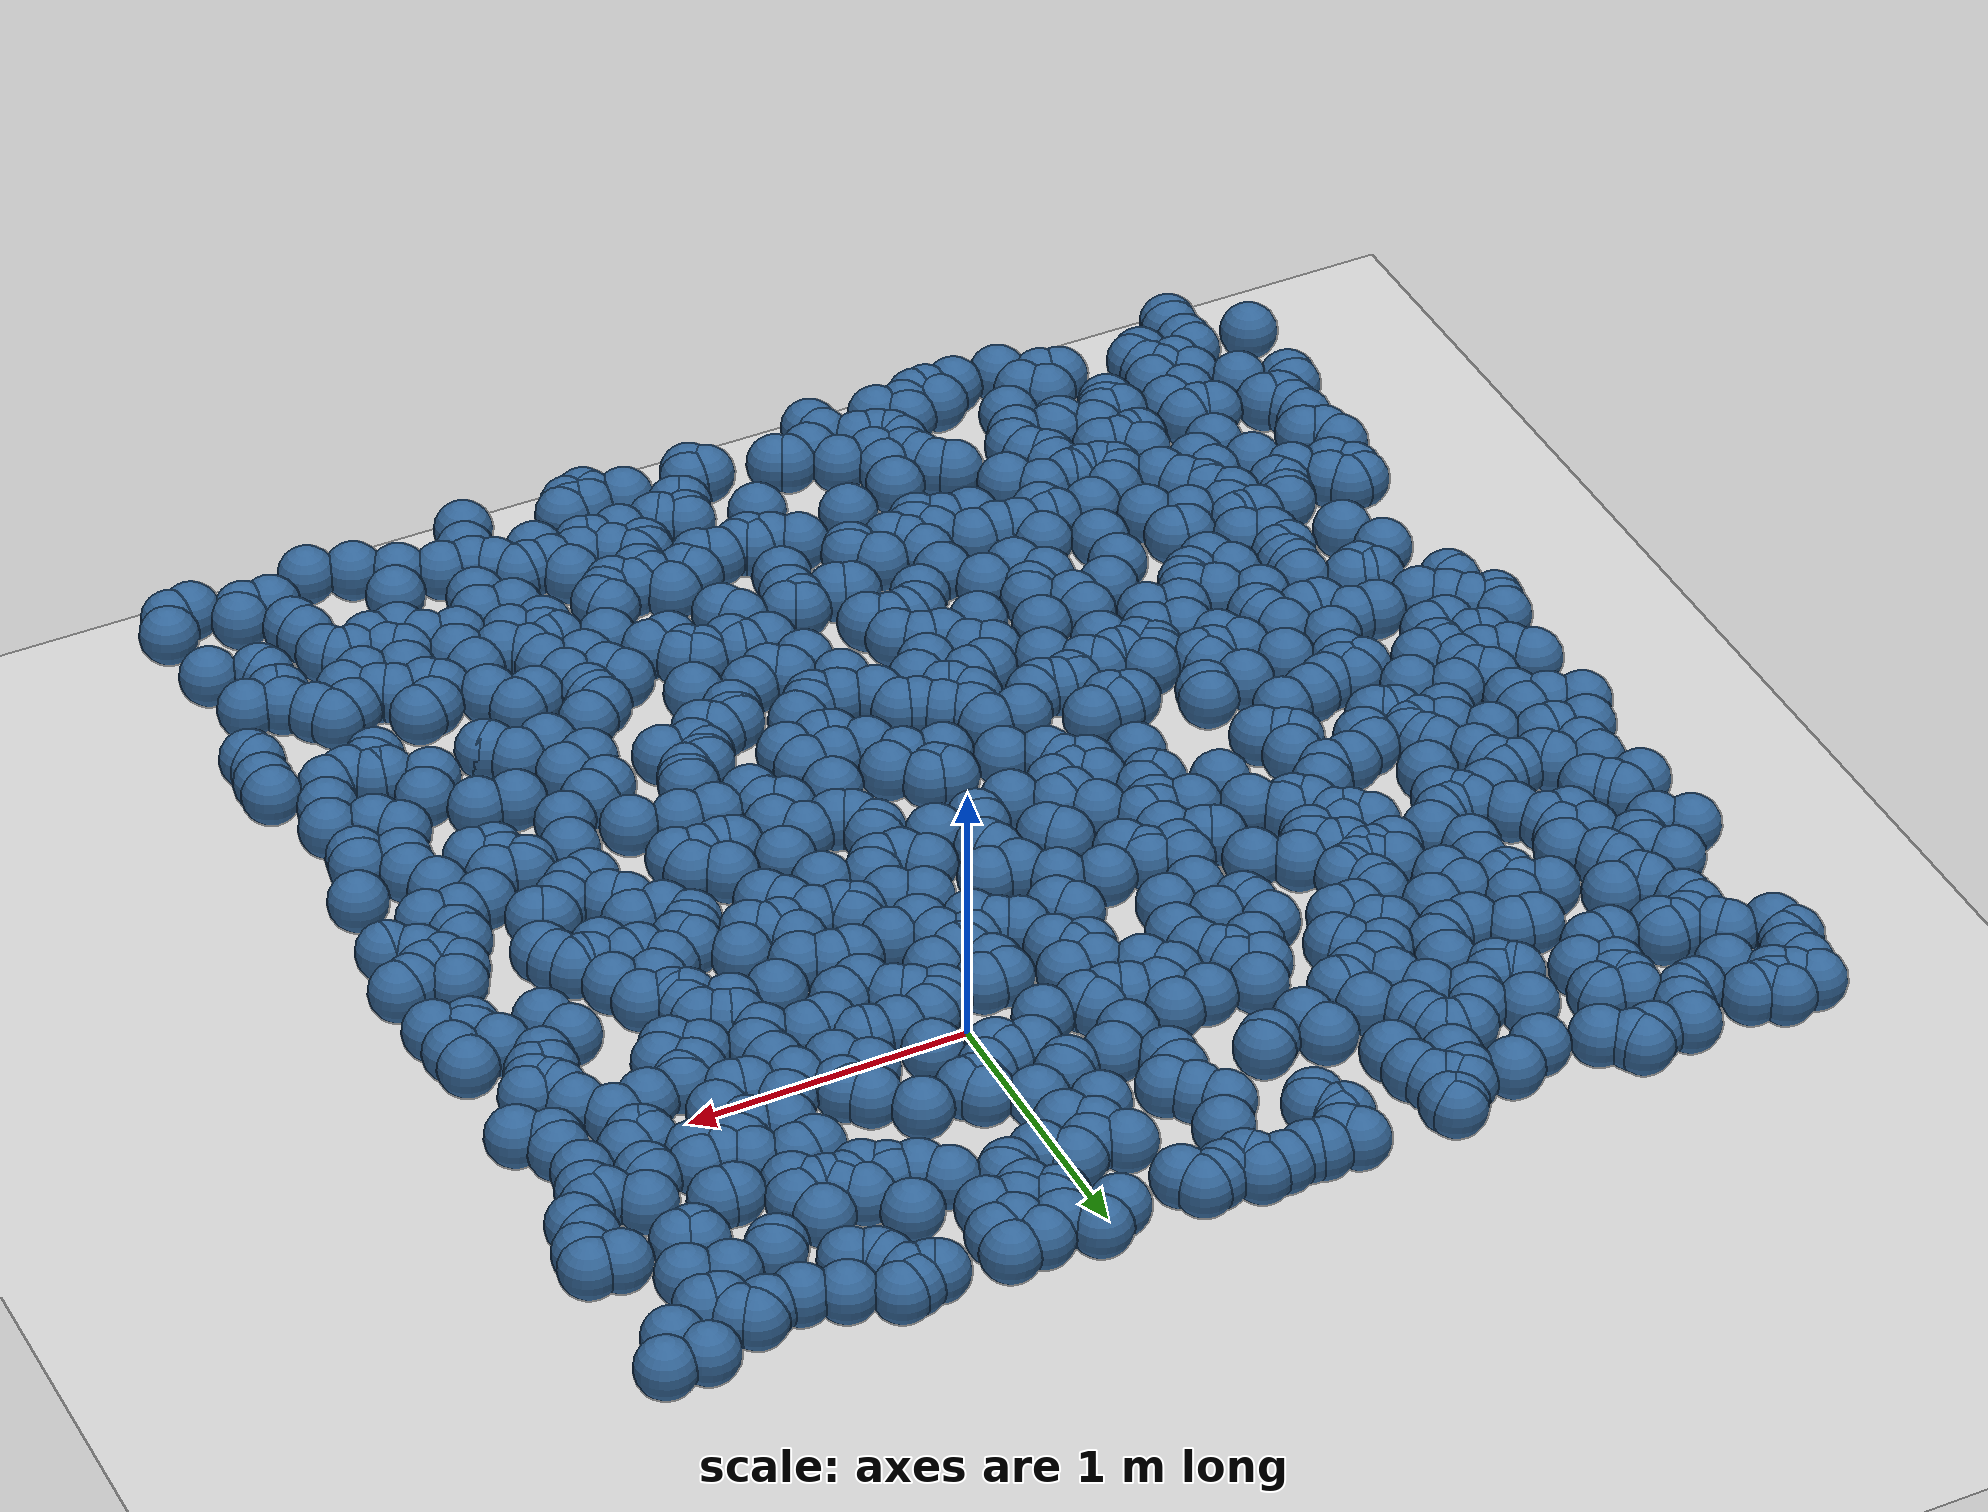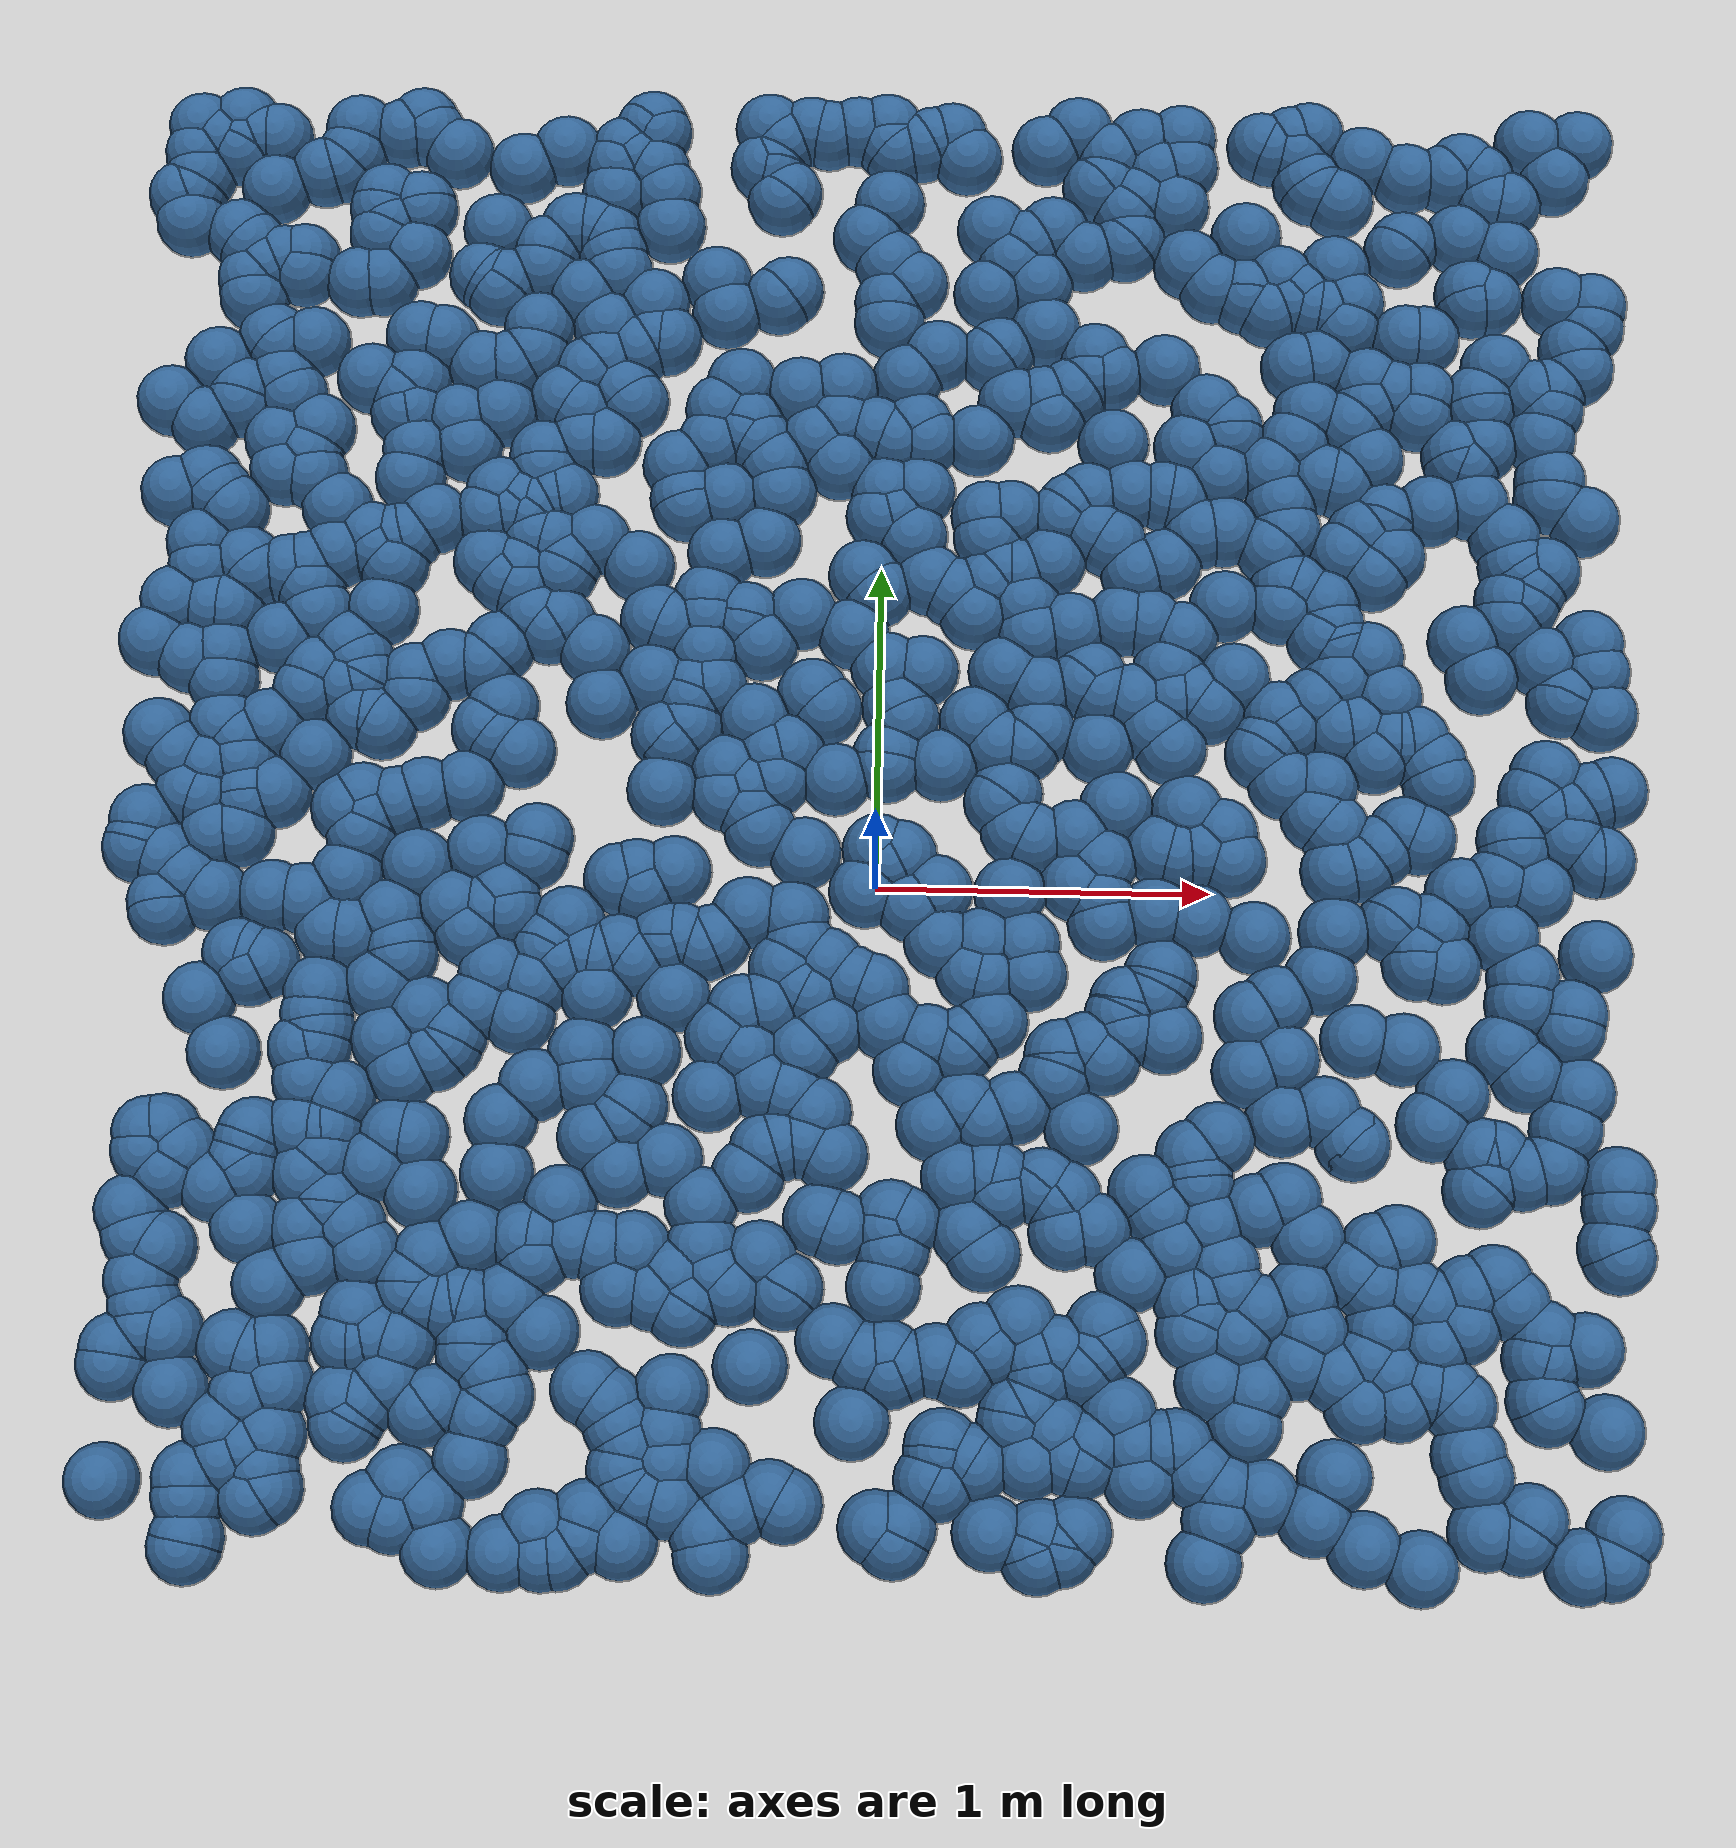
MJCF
<?xml version='1.0' encoding='utf-8'?>
<mujoco model="random_spheres">
  <option timestep="0.01" gravity="0 0 -9.81" />
  <worldbody>
    <geom name="floor" type="plane" size="50 50 0.1" pos="0 0 0" rgba="0.8 0.8 0.8 1" />
    <body name="sphere_0" pos="1.824 1.979 1.0">
      <geom type="sphere" size="0.1" rgba="0.2 0.4 0.6 1" />
      <freejoint />
    </body>
    <body name="sphere_1" pos="0.397 -1.380 1.0">
      <geom type="sphere" size="0.1" rgba="0.2 0.4 0.6 1" />
      <freejoint />
    </body>
    <body name="sphere_2" pos="0.444 -1.474 1.0">
      <geom type="sphere" size="0.1" rgba="0.2 0.4 0.6 1" />
      <freejoint />
    </body>
    <body name="sphere_3" pos="-0.998 0.854 1.0">
      <geom type="sphere" size="0.1" rgba="0.2 0.4 0.6 1" />
      <freejoint />
    </body>
    <body name="sphere_4" pos="0.831 0.499 1.0">
      <geom type="sphere" size="0.1" rgba="0.2 0.4 0.6 1" />
      <freejoint />
    </body>
    <body name="sphere_5" pos="-0.362 -1.304 1.0">
      <geom type="sphere" size="0.1" rgba="0.2 0.4 0.6 1" />
      <freejoint />
    </body>
    <body name="sphere_6" pos="-0.568 -1.840 1.0">
      <geom type="sphere" size="0.1" rgba="0.2 0.4 0.6 1" />
      <freejoint />
    </body>
    <body name="sphere_7" pos="0.420 0.503 1.0">
      <geom type="sphere" size="0.1" rgba="0.2 0.4 0.6 1" />
      <freejoint />
    </body>
    <body name="sphere_8" pos="-0.469 -1.335 1.0">
      <geom type="sphere" size="0.1" rgba="0.2 0.4 0.6 1" />
      <freejoint />
    </body>
    <body name="sphere_9" pos="0.694 -1.250 1.0">
      <geom type="sphere" size="0.1" rgba="0.2 0.4 0.6 1" />
      <freejoint />
    </body>
    <body name="sphere_10" pos="-1.605 -1.740 1.0">
      <geom type="sphere" size="0.1" rgba="0.2 0.4 0.6 1" />
      <freejoint />
    </body>
    <body name="sphere_11" pos="1.945 0.494 1.0">
      <geom type="sphere" size="0.1" rgba="0.2 0.4 0.6 1" />
      <freejoint />
    </body>
    <body name="sphere_12" pos="0.528 0.868 1.0">
      <geom type="sphere" size="0.1" rgba="0.2 0.4 0.6 1" />
      <freejoint />
    </body>
    <body name="sphere_13" pos="-1.266 0.345 1.0">
      <geom type="sphere" size="0.1" rgba="0.2 0.4 0.6 1" />
      <freejoint />
    </body>
    <body name="sphere_14" pos="-1.156 1.019 1.0">
      <geom type="sphere" size="0.1" rgba="0.2 0.4 0.6 1" />
      <freejoint />
    </body>
    <body name="sphere_15" pos="-0.279 0.896 1.0">
      <geom type="sphere" size="0.1" rgba="0.2 0.4 0.6 1" />
      <freejoint />
    </body>
    <body name="sphere_16" pos="-1.127 1.525 1.0">
      <geom type="sphere" size="0.1" rgba="0.2 0.4 0.6 1" />
      <freejoint />
    </body>
    <body name="sphere_17" pos="1.868 -0.538 1.0">
      <geom type="sphere" size="0.1" rgba="0.2 0.4 0.6 1" />
      <freejoint />
    </body>
    <body name="sphere_18" pos="-0.232 1.195 1.0">
      <geom type="sphere" size="0.1" rgba="0.2 0.4 0.6 1" />
      <freejoint />
    </body>
    <body name="sphere_19" pos="0.847 -1.313 1.0">
      <geom type="sphere" size="0.1" rgba="0.2 0.4 0.6 1" />
      <freejoint />
    </body>
    <body name="sphere_20" pos="-1.320 -0.509 1.0">
      <geom type="sphere" size="0.1" rgba="0.2 0.4 0.6 1" />
      <freejoint />
    </body>
    <body name="sphere_21" pos="-1.335 -1.386 1.0">
      <geom type="sphere" size="0.1" rgba="0.2 0.4 0.6 1" />
      <freejoint />
    </body>
    <body name="sphere_22" pos="1.975 0.296 1.0">
      <geom type="sphere" size="0.1" rgba="0.2 0.4 0.6 1" />
      <freejoint />
    </body>
    <body name="sphere_23" pos="-1.622 -0.271 1.0">
      <geom type="sphere" size="0.1" rgba="0.2 0.4 0.6 1" />
      <freejoint />
    </body>
    <body name="sphere_24" pos="0.443 -1.963 1.0">
      <geom type="sphere" size="0.1" rgba="0.2 0.4 0.6 1" />
      <freejoint />
    </body>
    <body name="sphere_25" pos="1.432 -0.042 1.0">
      <geom type="sphere" size="0.1" rgba="0.2 0.4 0.6 1" />
      <freejoint />
    </body>
    <body name="sphere_26" pos="0.013 1.466 1.0">
      <geom type="sphere" size="0.1" rgba="0.2 0.4 0.6 1" />
      <freejoint />
    </body>
    <body name="sphere_27" pos="-0.178 0.319 1.0">
      <geom type="sphere" size="0.1" rgba="0.2 0.4 0.6 1" />
      <freejoint />
    </body>
    <body name="sphere_28" pos="0.184 -1.482 1.0">
      <geom type="sphere" size="0.1" rgba="0.2 0.4 0.6 1" />
      <freejoint />
    </body>
    <body name="sphere_29" pos="1.288 1.415 1.0">
      <geom type="sphere" size="0.1" rgba="0.2 0.4 0.6 1" />
      <freejoint />
    </body>
    <body name="sphere_30" pos="-0.615 0.355 1.0">
      <geom type="sphere" size="0.1" rgba="0.2 0.4 0.6 1" />
      <freejoint />
    </body>
    <body name="sphere_31" pos="-0.877 -1.185 1.0">
      <geom type="sphere" size="0.1" rgba="0.2 0.4 0.6 1" />
      <freejoint />
    </body>
    <body name="sphere_32" pos="1.586 1.872 1.0">
      <geom type="sphere" size="0.1" rgba="0.2 0.4 0.6 1" />
      <freejoint />
    </body>
    <body name="sphere_33" pos="1.765 -1.558 1.0">
      <geom type="sphere" size="0.1" rgba="0.2 0.4 0.6 1" />
      <freejoint />
    </body>
    <body name="sphere_34" pos="1.854 0.966 1.0">
      <geom type="sphere" size="0.1" rgba="0.2 0.4 0.6 1" />
      <freejoint />
    </body>
    <body name="sphere_35" pos="-1.151 -1.632 1.0">
      <geom type="sphere" size="0.1" rgba="0.2 0.4 0.6 1" />
      <freejoint />
    </body>
    <body name="sphere_36" pos="-0.642 -0.196 1.0">
      <geom type="sphere" size="0.1" rgba="0.2 0.4 0.6 1" />
      <freejoint />
    </body>
    <body name="sphere_37" pos="-0.103 -0.950 1.0">
      <geom type="sphere" size="0.1" rgba="0.2 0.4 0.6 1" />
      <freejoint />
    </body>
    <body name="sphere_38" pos="1.259 0.378 1.0">
      <geom type="sphere" size="0.1" rgba="0.2 0.4 0.6 1" />
      <freejoint />
    </body>
    <body name="sphere_39" pos="-0.182 -0.668 1.0">
      <geom type="sphere" size="0.1" rgba="0.2 0.4 0.6 1" />
      <freejoint />
    </body>
    <body name="sphere_40" pos="-0.458 -0.387 1.0">
      <geom type="sphere" size="0.1" rgba="0.2 0.4 0.6 1" />
      <freejoint />
    </body>
    <body name="sphere_41" pos="-0.403 -1.933 1.0">
      <geom type="sphere" size="0.1" rgba="0.2 0.4 0.6 1" />
      <freejoint />
    </body>
    <body name="sphere_42" pos="-0.274 -0.934 1.0">
      <geom type="sphere" size="0.1" rgba="0.2 0.4 0.6 1" />
      <freejoint />
    </body>
    <body name="sphere_43" pos="-1.503 1.968 1.0">
      <geom type="sphere" size="0.1" rgba="0.2 0.4 0.6 1" />
      <freejoint />
    </body>
    <body name="sphere_44" pos="-0.283 1.790 1.0">
      <geom type="sphere" size="0.1" rgba="0.2 0.4 0.6 1" />
      <freejoint />
    </body>
    <body name="sphere_45" pos="-1.786 1.168 1.0">
      <geom type="sphere" size="0.1" rgba="0.2 0.4 0.6 1" />
      <freejoint />
    </body>
    <body name="sphere_46" pos="0.042 -1.293 1.0">
      <geom type="sphere" size="0.1" rgba="0.2 0.4 0.6 1" />
      <freejoint />
    </body>
    <body name="sphere_47" pos="-1.832 1.986 1.0">
      <geom type="sphere" size="0.1" rgba="0.2 0.4 0.6 1" />
      <freejoint />
    </body>
    <body name="sphere_48" pos="-0.781 0.435 1.0">
      <geom type="sphere" size="0.1" rgba="0.2 0.4 0.6 1" />
      <freejoint />
    </body>
    <body name="sphere_49" pos="1.819 0.445 1.0">
      <geom type="sphere" size="0.1" rgba="0.2 0.4 0.6 1" />
      <freejoint />
    </body>
    <body name="sphere_50" pos="-0.286 0.149 1.0">
      <geom type="sphere" size="0.1" rgba="0.2 0.4 0.6 1" />
      <freejoint />
    </body>
    <body name="sphere_51" pos="0.013 1.406 1.0">
      <geom type="sphere" size="0.1" rgba="0.2 0.4 0.6 1" />
      <freejoint />
    </body>
    <body name="sphere_52" pos="0.902 1.165 1.0">
      <geom type="sphere" size="0.1" rgba="0.2 0.4 0.6 1" />
      <freejoint />
    </body>
    <body name="sphere_53" pos="1.742 -0.436 1.0">
      <geom type="sphere" size="0.1" rgba="0.2 0.4 0.6 1" />
      <freejoint />
    </body>
    <body name="sphere_54" pos="-0.433 0.881 1.0">
      <geom type="sphere" size="0.1" rgba="0.2 0.4 0.6 1" />
      <freejoint />
    </body>
    <body name="sphere_55" pos="-0.777 1.284 1.0">
      <geom type="sphere" size="0.1" rgba="0.2 0.4 0.6 1" />
      <freejoint />
    </body>
    <body name="sphere_56" pos="-1.989 0.442 1.0">
      <geom type="sphere" size="0.1" rgba="0.2 0.4 0.6 1" />
      <freejoint />
    </body>
    <body name="sphere_57" pos="0.500 -1.455 1.0">
      <geom type="sphere" size="0.1" rgba="0.2 0.4 0.6 1" />
      <freejoint />
    </body>
    <body name="sphere_58" pos="0.422 -0.453 1.0">
      <geom type="sphere" size="0.1" rgba="0.2 0.4 0.6 1" />
      <freejoint />
    </body>
    <body name="sphere_59" pos="1.279 0.745 1.0">
      <geom type="sphere" size="0.1" rgba="0.2 0.4 0.6 1" />
      <freejoint />
    </body>
    <body name="sphere_60" pos="-1.297 -0.005 1.0">
      <geom type="sphere" size="0.1" rgba="0.2 0.4 0.6 1" />
      <freejoint />
    </body>
    <body name="sphere_61" pos="-1.989 -0.128 1.0">
      <geom type="sphere" size="0.1" rgba="0.2 0.4 0.6 1" />
      <freejoint />
    </body>
    <body name="sphere_62" pos="1.280 -0.895 1.0">
      <geom type="sphere" size="0.1" rgba="0.2 0.4 0.6 1" />
      <freejoint />
    </body>
    <body name="sphere_63" pos="1.961 1.978 1.0">
      <geom type="sphere" size="0.1" rgba="0.2 0.4 0.6 1" />
      <freejoint />
    </body>
    <body name="sphere_64" pos="0.012 0.906 1.0">
      <geom type="sphere" size="0.1" rgba="0.2 0.4 0.6 1" />
      <freejoint />
    </body>
    <body name="sphere_65" pos="1.561 -1.373 1.0">
      <geom type="sphere" size="0.1" rgba="0.2 0.4 0.6 1" />
      <freejoint />
    </body>
    <body name="sphere_66" pos="1.870 0.333 1.0">
      <geom type="sphere" size="0.1" rgba="0.2 0.4 0.6 1" />
      <freejoint />
    </body>
    <body name="sphere_67" pos="-1.422 1.724 1.0">
      <geom type="sphere" size="0.1" rgba="0.2 0.4 0.6 1" />
      <freejoint />
    </body>
    <body name="sphere_68" pos="-1.704 -0.432 1.0">
      <geom type="sphere" size="0.1" rgba="0.2 0.4 0.6 1" />
      <freejoint />
    </body>
    <body name="sphere_69" pos="-1.727 0.104 1.0">
      <geom type="sphere" size="0.1" rgba="0.2 0.4 0.6 1" />
      <freejoint />
    </body>
    <body name="sphere_70" pos="-1.640 1.532 1.0">
      <geom type="sphere" size="0.1" rgba="0.2 0.4 0.6 1" />
      <freejoint />
    </body>
    <body name="sphere_71" pos="-1.196 -1.818 1.0">
      <geom type="sphere" size="0.1" rgba="0.2 0.4 0.6 1" />
      <freejoint />
    </body>
    <body name="sphere_72" pos="0.234 -1.000 1.0">
      <geom type="sphere" size="0.1" rgba="0.2 0.4 0.6 1" />
      <freejoint />
    </body>
    <body name="sphere_73" pos="0.678 -0.523 1.0">
      <geom type="sphere" size="0.1" rgba="0.2 0.4 0.6 1" />
      <freejoint />
    </body>
    <body name="sphere_74" pos="-1.479 -0.631 1.0">
      <geom type="sphere" size="0.1" rgba="0.2 0.4 0.6 1" />
      <freejoint />
    </body>
    <body name="sphere_75" pos="-0.732 -0.908 1.0">
      <geom type="sphere" size="0.1" rgba="0.2 0.4 0.6 1" />
      <freejoint />
    </body>
    <body name="sphere_76" pos="0.675 1.648 1.0">
      <geom type="sphere" size="0.1" rgba="0.2 0.4 0.6 1" />
      <freejoint />
    </body>
    <body name="sphere_77" pos="-0.508 -1.855 1.0">
      <geom type="sphere" size="0.1" rgba="0.2 0.4 0.6 1" />
      <freejoint />
    </body>
    <body name="sphere_78" pos="-1.743 1.545 1.0">
      <geom type="sphere" size="0.1" rgba="0.2 0.4 0.6 1" />
      <freejoint />
    </body>
    <body name="sphere_79" pos="-1.431 1.215 1.0">
      <geom type="sphere" size="0.1" rgba="0.2 0.4 0.6 1" />
      <freejoint />
    </body>
    <body name="sphere_80" pos="-1.034 0.637 1.0">
      <geom type="sphere" size="0.1" rgba="0.2 0.4 0.6 1" />
      <freejoint />
    </body>
    <body name="sphere_81" pos="-0.472 0.535 1.0">
      <geom type="sphere" size="0.1" rgba="0.2 0.4 0.6 1" />
      <freejoint />
    </body>
    <body name="sphere_82" pos="-0.170 -0.512 1.0">
      <geom type="sphere" size="0.1" rgba="0.2 0.4 0.6 1" />
      <freejoint />
    </body>
    <body name="sphere_83" pos="1.693 -1.310 1.0">
      <geom type="sphere" size="0.1" rgba="0.2 0.4 0.6 1" />
      <freejoint />
    </body>
    <body name="sphere_84" pos="-1.575 -1.862 1.0">
      <geom type="sphere" size="0.1" rgba="0.2 0.4 0.6 1" />
      <freejoint />
    </body>
    <body name="sphere_85" pos="-1.631 0.017 1.0">
      <geom type="sphere" size="0.1" rgba="0.2 0.4 0.6 1" />
      <freejoint />
    </body>
    <body name="sphere_86" pos="-0.213 -1.303 1.0">
      <geom type="sphere" size="0.1" rgba="0.2 0.4 0.6 1" />
      <freejoint />
    </body>
    <body name="sphere_87" pos="1.640 -0.923 1.0">
      <geom type="sphere" size="0.1" rgba="0.2 0.4 0.6 1" />
      <freejoint />
    </body>
    <body name="sphere_88" pos="0.077 -1.946 1.0">
      <geom type="sphere" size="0.1" rgba="0.2 0.4 0.6 1" />
      <freejoint />
    </body>
    <body name="sphere_89" pos="-1.185 -1.064 1.0">
      <geom type="sphere" size="0.1" rgba="0.2 0.4 0.6 1" />
      <freejoint />
    </body>
    <body name="sphere_90" pos="-0.019 1.082 1.0">
      <geom type="sphere" size="0.1" rgba="0.2 0.4 0.6 1" />
      <freejoint />
    </body>
    <body name="sphere_91" pos="-0.724 -1.569 1.0">
      <geom type="sphere" size="0.1" rgba="0.2 0.4 0.6 1" />
      <freejoint />
    </body>
    <body name="sphere_92" pos="-1.828 0.003 1.0">
      <geom type="sphere" size="0.1" rgba="0.2 0.4 0.6 1" />
      <freejoint />
    </body>
    <body name="sphere_93" pos="0.151 1.311 1.0">
      <geom type="sphere" size="0.1" rgba="0.2 0.4 0.6 1" />
      <freejoint />
    </body>
    <body name="sphere_94" pos="-1.411 -0.368 1.0">
      <geom type="sphere" size="0.1" rgba="0.2 0.4 0.6 1" />
      <freejoint />
    </body>
    <body name="sphere_95" pos="-1.372 -0.041 1.0">
      <geom type="sphere" size="0.1" rgba="0.2 0.4 0.6 1" />
      <freejoint />
    </body>
    <body name="sphere_96" pos="-1.419 1.647 1.0">
      <geom type="sphere" size="0.1" rgba="0.2 0.4 0.6 1" />
      <freejoint />
    </body>
    <body name="sphere_97" pos="-0.402 -0.634 1.0">
      <geom type="sphere" size="0.1" rgba="0.2 0.4 0.6 1" />
      <freejoint />
    </body>
    <body name="sphere_98" pos="-1.643 0.455 1.0">
      <geom type="sphere" size="0.1" rgba="0.2 0.4 0.6 1" />
      <freejoint />
    </body>
    <body name="sphere_99" pos="0.510 -1.958 1.0">
      <geom type="sphere" size="0.1" rgba="0.2 0.4 0.6 1" />
      <freejoint />
    </body>
    <body name="sphere_100" pos="-1.662 -0.997 1.0">
      <geom type="sphere" size="0.1" rgba="0.2 0.4 0.6 1" />
      <freejoint />
    </body>
    <body name="sphere_101" pos="-1.054 -0.560 1.0">
      <geom type="sphere" size="0.1" rgba="0.2 0.4 0.6 1" />
      <freejoint />
    </body>
    <body name="sphere_102" pos="-0.407 0.100 1.0">
      <geom type="sphere" size="0.1" rgba="0.2 0.4 0.6 1" />
      <freejoint />
    </body>
    <body name="sphere_103" pos="0.428 1.526 1.0">
      <geom type="sphere" size="0.1" rgba="0.2 0.4 0.6 1" />
      <freejoint />
    </body>
    <body name="sphere_104" pos="-1.456 0.322 1.0">
      <geom type="sphere" size="0.1" rgba="0.2 0.4 0.6 1" />
      <freejoint />
    </body>
    <body name="sphere_105" pos="-1.485 -0.678 1.0">
      <geom type="sphere" size="0.1" rgba="0.2 0.4 0.6 1" />
      <freejoint />
    </body>
    <body name="sphere_106" pos="-1.859 -0.223 1.0">
      <geom type="sphere" size="0.1" rgba="0.2 0.4 0.6 1" />
      <freejoint />
    </body>
    <body name="sphere_107" pos="-1.748 -1.991 1.0">
      <geom type="sphere" size="0.1" rgba="0.2 0.4 0.6 1" />
      <freejoint />
    </body>
    <body name="sphere_108" pos="1.341 0.450 1.0">
      <geom type="sphere" size="0.1" rgba="0.2 0.4 0.6 1" />
      <freejoint />
    </body>
    <body name="sphere_109" pos="1.077 1.458 1.0">
      <geom type="sphere" size="0.1" rgba="0.2 0.4 0.6 1" />
      <freejoint />
    </body>
    <body name="sphere_110" pos="0.503 0.839 1.0">
      <geom type="sphere" size="0.1" rgba="0.2 0.4 0.6 1" />
      <freejoint />
    </body>
    <body name="sphere_111" pos="-1.634 -0.917 1.0">
      <geom type="sphere" size="0.1" rgba="0.2 0.4 0.6 1" />
      <freejoint />
    </body>
    <body name="sphere_112" pos="1.197 1.469 1.0">
      <geom type="sphere" size="0.1" rgba="0.2 0.4 0.6 1" />
      <freejoint />
    </body>
    <body name="sphere_113" pos="0.618 -1.390 1.0">
      <geom type="sphere" size="0.1" rgba="0.2 0.4 0.6 1" />
      <freejoint />
    </body>
    <body name="sphere_114" pos="0.264 -1.148 1.0">
      <geom type="sphere" size="0.1" rgba="0.2 0.4 0.6 1" />
      <freejoint />
    </body>
    <body name="sphere_115" pos="0.950 0.590 1.0">
      <geom type="sphere" size="0.1" rgba="0.2 0.4 0.6 1" />
      <freejoint />
    </body>
    <body name="sphere_116" pos="0.584 -1.696 1.0">
      <geom type="sphere" size="0.1" rgba="0.2 0.4 0.6 1" />
      <freejoint />
    </body>
    <body name="sphere_117" pos="-0.560 -0.368 1.0">
      <geom type="sphere" size="0.1" rgba="0.2 0.4 0.6 1" />
      <freejoint />
    </body>
    <body name="sphere_118" pos="0.150 -0.635 1.0">
      <geom type="sphere" size="0.1" rgba="0.2 0.4 0.6 1" />
      <freejoint />
    </body>
    <body name="sphere_119" pos="1.751 1.790 1.0">
      <geom type="sphere" size="0.1" rgba="0.2 0.4 0.6 1" />
      <freejoint />
    </body>
    <body name="sphere_120" pos="-1.152 -1.234 1.0">
      <geom type="sphere" size="0.1" rgba="0.2 0.4 0.6 1" />
      <freejoint />
    </body>
    <body name="sphere_121" pos="1.220 0.600 1.0">
      <geom type="sphere" size="0.1" rgba="0.2 0.4 0.6 1" />
      <freejoint />
    </body>
    <body name="sphere_122" pos="1.187 1.156 1.0">
      <geom type="sphere" size="0.1" rgba="0.2 0.4 0.6 1" />
      <freejoint />
    </body>
    <body name="sphere_123" pos="-0.728 -1.948 1.0">
      <geom type="sphere" size="0.1" rgba="0.2 0.4 0.6 1" />
      <freejoint />
    </body>
    <body name="sphere_124" pos="-0.243 -1.840 1.0">
      <geom type="sphere" size="0.1" rgba="0.2 0.4 0.6 1" />
      <freejoint />
    </body>
    <body name="sphere_125" pos="-1.267 0.296 1.0">
      <geom type="sphere" size="0.1" rgba="0.2 0.4 0.6 1" />
      <freejoint />
    </body>
    <body name="sphere_126" pos="1.106 0.889 1.0">
      <geom type="sphere" size="0.1" rgba="0.2 0.4 0.6 1" />
      <freejoint />
    </body>
    <body name="sphere_127" pos="1.268 0.954 1.0">
      <geom type="sphere" size="0.1" rgba="0.2 0.4 0.6 1" />
      <freejoint />
    </body>
    <body name="sphere_128" pos="-0.970 1.377 1.0">
      <geom type="sphere" size="0.1" rgba="0.2 0.4 0.6 1" />
      <freejoint />
    </body>
    <body name="sphere_129" pos="1.617 -0.915 1.0">
      <geom type="sphere" size="0.1" rgba="0.2 0.4 0.6 1" />
      <freejoint />
    </body>
    <body name="sphere_130" pos="-1.636 -0.456 1.0">
      <geom type="sphere" size="0.1" rgba="0.2 0.4 0.6 1" />
      <freejoint />
    </body>
    <body name="sphere_131" pos="0.322 -1.451 1.0">
      <geom type="sphere" size="0.1" rgba="0.2 0.4 0.6 1" />
      <freejoint />
    </body>
    <body name="sphere_132" pos="1.680 -0.179 1.0">
      <geom type="sphere" size="0.1" rgba="0.2 0.4 0.6 1" />
      <freejoint />
    </body>
    <body name="sphere_133" pos="0.266 0.248 1.0">
      <geom type="sphere" size="0.1" rgba="0.2 0.4 0.6 1" />
      <freejoint />
    </body>
    <body name="sphere_134" pos="1.546 -1.577 1.0">
      <geom type="sphere" size="0.1" rgba="0.2 0.4 0.6 1" />
      <freejoint />
    </body>
    <body name="sphere_135" pos="-0.580 0.510 1.0">
      <geom type="sphere" size="0.1" rgba="0.2 0.4 0.6 1" />
      <freejoint />
    </body>
    <body name="sphere_136" pos="-1.353 0.215 1.0">
      <geom type="sphere" size="0.1" rgba="0.2 0.4 0.6 1" />
      <freejoint />
    </body>
    <body name="sphere_137" pos="1.845 -0.847 1.0">
      <geom type="sphere" size="0.1" rgba="0.2 0.4 0.6 1" />
      <freejoint />
    </body>
    <body name="sphere_138" pos="0.250 -0.636 1.0">
      <geom type="sphere" size="0.1" rgba="0.2 0.4 0.6 1" />
      <freejoint />
    </body>
    <body name="sphere_139" pos="0.490 -0.728 1.0">
      <geom type="sphere" size="0.1" rgba="0.2 0.4 0.6 1" />
      <freejoint />
    </body>
    <body name="sphere_140" pos="0.699 -1.695 1.0">
      <geom type="sphere" size="0.1" rgba="0.2 0.4 0.6 1" />
      <freejoint />
    </body>
    <body name="sphere_141" pos="-1.038 0.186 1.0">
      <geom type="sphere" size="0.1" rgba="0.2 0.4 0.6 1" />
      <freejoint />
    </body>
    <body name="sphere_142" pos="0.226 1.905 1.0">
      <geom type="sphere" size="0.1" rgba="0.2 0.4 0.6 1" />
      <freejoint />
    </body>
    <body name="sphere_143" pos="0.299 0.776 1.0">
      <geom type="sphere" size="0.1" rgba="0.2 0.4 0.6 1" />
      <freejoint />
    </body>
    <body name="sphere_144" pos="1.097 -1.044 1.0">
      <geom type="sphere" size="0.1" rgba="0.2 0.4 0.6 1" />
      <freejoint />
    </body>
    <body name="sphere_145" pos="1.192 0.318 1.0">
      <geom type="sphere" size="0.1" rgba="0.2 0.4 0.6 1" />
      <freejoint />
    </body>
    <body name="sphere_146" pos="-0.281 -0.548 1.0">
      <geom type="sphere" size="0.1" rgba="0.2 0.4 0.6 1" />
      <freejoint />
    </body>
    <body name="sphere_147" pos="-0.118 -0.607 1.0">
      <geom type="sphere" size="0.1" rgba="0.2 0.4 0.6 1" />
      <freejoint />
    </body>
    <body name="sphere_148" pos="-0.404 -1.267 1.0">
      <geom type="sphere" size="0.1" rgba="0.2 0.4 0.6 1" />
      <freejoint />
    </body>
    <body name="sphere_149" pos="-0.847 1.479 1.0">
      <geom type="sphere" size="0.1" rgba="0.2 0.4 0.6 1" />
      <freejoint />
    </body>
    <body name="sphere_150" pos="-0.373 1.100 1.0">
      <geom type="sphere" size="0.1" rgba="0.2 0.4 0.6 1" />
      <freejoint />
    </body>
    <body name="sphere_151" pos="1.952 -0.114 1.0">
      <geom type="sphere" size="0.1" rgba="0.2 0.4 0.6 1" />
      <freejoint />
    </body>
    <body name="sphere_152" pos="0.166 -0.862 1.0">
      <geom type="sphere" size="0.1" rgba="0.2 0.4 0.6 1" />
      <freejoint />
    </body>
    <body name="sphere_153" pos="-1.085 -0.360 1.0">
      <geom type="sphere" size="0.1" rgba="0.2 0.4 0.6 1" />
      <freejoint />
    </body>
    <body name="sphere_154" pos="-0.183 1.058 1.0">
      <geom type="sphere" size="0.1" rgba="0.2 0.4 0.6 1" />
      <freejoint />
    </body>
    <body name="sphere_155" pos="0.299 1.690 1.0">
      <geom type="sphere" size="0.1" rgba="0.2 0.4 0.6 1" />
      <freejoint />
    </body>
    <body name="sphere_156" pos="-0.611 1.344 1.0">
      <geom type="sphere" size="0.1" rgba="0.2 0.4 0.6 1" />
      <freejoint />
    </body>
    <body name="sphere_157" pos="1.063 1.958 1.0">
      <geom type="sphere" size="0.1" rgba="0.2 0.4 0.6 1" />
      <freejoint />
    </body>
    <body name="sphere_158" pos="0.035 0.843 1.0">
      <geom type="sphere" size="0.1" rgba="0.2 0.4 0.6 1" />
      <freejoint />
    </body>
    <body name="sphere_159" pos="1.818 1.223 1.0">
      <geom type="sphere" size="0.1" rgba="0.2 0.4 0.6 1" />
      <freejoint />
    </body>
    <body name="sphere_160" pos="1.095 0.277 1.0">
      <geom type="sphere" size="0.1" rgba="0.2 0.4 0.6 1" />
      <freejoint />
    </body>
    <body name="sphere_161" pos="1.676 1.872 1.0">
      <geom type="sphere" size="0.1" rgba="0.2 0.4 0.6 1" />
      <freejoint />
    </body>
    <body name="sphere_162" pos="0.586 1.255 1.0">
      <geom type="sphere" size="0.1" rgba="0.2 0.4 0.6 1" />
      <freejoint />
    </body>
    <body name="sphere_163" pos="-1.898 0.118 1.0">
      <geom type="sphere" size="0.1" rgba="0.2 0.4 0.6 1" />
      <freejoint />
    </body>
    <body name="sphere_164" pos="-0.519 -0.369 1.0">
      <geom type="sphere" size="0.1" rgba="0.2 0.4 0.6 1" />
      <freejoint />
    </body>
    <body name="sphere_165" pos="-0.687 1.316 1.0">
      <geom type="sphere" size="0.1" rgba="0.2 0.4 0.6 1" />
      <freejoint />
    </body>
    <body name="sphere_166" pos="-1.496 -0.772 1.0">
      <geom type="sphere" size="0.1" rgba="0.2 0.4 0.6 1" />
      <freejoint />
    </body>
    <body name="sphere_167" pos="1.209 0.083 1.0">
      <geom type="sphere" size="0.1" rgba="0.2 0.4 0.6 1" />
      <freejoint />
    </body>
    <body name="sphere_168" pos="-0.560 -0.383 1.0">
      <geom type="sphere" size="0.1" rgba="0.2 0.4 0.6 1" />
      <freejoint />
    </body>
    <body name="sphere_169" pos="1.078 0.756 1.0">
      <geom type="sphere" size="0.1" rgba="0.2 0.4 0.6 1" />
      <freejoint />
    </body>
    <body name="sphere_170" pos="0.541 1.996 1.0">
      <geom type="sphere" size="0.1" rgba="0.2 0.4 0.6 1" />
      <freejoint />
    </body>
    <body name="sphere_171" pos="1.620 1.014 1.0">
      <geom type="sphere" size="0.1" rgba="0.2 0.4 0.6 1" />
      <freejoint />
    </body>
    <body name="sphere_172" pos="0.121 0.389 1.0">
      <geom type="sphere" size="0.1" rgba="0.2 0.4 0.6 1" />
      <freejoint />
    </body>
    <body name="sphere_173" pos="0.852 1.598 1.0">
      <geom type="sphere" size="0.1" rgba="0.2 0.4 0.6 1" />
      <freejoint />
    </body>
    <body name="sphere_174" pos="0.100 -0.268 1.0">
      <geom type="sphere" size="0.1" rgba="0.2 0.4 0.6 1" />
      <freejoint />
    </body>
    <body name="sphere_175" pos="0.009 -0.115 1.0">
      <geom type="sphere" size="0.1" rgba="0.2 0.4 0.6 1" />
      <freejoint />
    </body>
    <body name="sphere_176" pos="0.810 -1.691 1.0">
      <geom type="sphere" size="0.1" rgba="0.2 0.4 0.6 1" />
      <freejoint />
    </body>
    <body name="sphere_177" pos="-0.915 -0.101 1.0">
      <geom type="sphere" size="0.1" rgba="0.2 0.4 0.6 1" />
      <freejoint />
    </body>
    <body name="sphere_178" pos="1.401 0.212 1.0">
      <geom type="sphere" size="0.1" rgba="0.2 0.4 0.6 1" />
      <freejoint />
    </body>
    <body name="sphere_179" pos="1.483 -1.416 1.0">
      <geom type="sphere" size="0.1" rgba="0.2 0.4 0.6 1" />
      <freejoint />
    </body>
    <body name="sphere_180" pos="0.032 -1.912 1.0">
      <geom type="sphere" size="0.1" rgba="0.2 0.4 0.6 1" />
      <freejoint />
    </body>
    <body name="sphere_181" pos="-1.410 0.240 1.0">
      <geom type="sphere" size="0.1" rgba="0.2 0.4 0.6 1" />
      <freejoint />
    </body>
    <body name="sphere_182" pos="1.944 0.853 1.0">
      <geom type="sphere" size="0.1" rgba="0.2 0.4 0.6 1" />
      <freejoint />
    </body>
    <body name="sphere_183" pos="1.364 -0.094 1.0">
      <geom type="sphere" size="0.1" rgba="0.2 0.4 0.6 1" />
      <freejoint />
    </body>
    <body name="sphere_184" pos="1.426 -1.288 1.0">
      <geom type="sphere" size="0.1" rgba="0.2 0.4 0.6 1" />
      <freejoint />
    </body>
    <body name="sphere_185" pos="0.039 -0.592 1.0">
      <geom type="sphere" size="0.1" rgba="0.2 0.4 0.6 1" />
      <freejoint />
    </body>
    <body name="sphere_186" pos="0.666 0.544 1.0">
      <geom type="sphere" size="0.1" rgba="0.2 0.4 0.6 1" />
      <freejoint />
    </body>
    <body name="sphere_187" pos="1.979 -1.052 1.0">
      <geom type="sphere" size="0.1" rgba="0.2 0.4 0.6 1" />
      <freejoint />
    </body>
    <body name="sphere_188" pos="0.619 -0.678 1.0">
      <geom type="sphere" size="0.1" rgba="0.2 0.4 0.6 1" />
      <freejoint />
    </body>
    <body name="sphere_189" pos="-0.435 0.721 1.0">
      <geom type="sphere" size="0.1" rgba="0.2 0.4 0.6 1" />
      <freejoint />
    </body>
    <body name="sphere_190" pos="-0.001 -0.499 1.0">
      <geom type="sphere" size="0.1" rgba="0.2 0.4 0.6 1" />
      <freejoint />
    </body>
    <body name="sphere_191" pos="-1.794 1.137 1.0">
      <geom type="sphere" size="0.1" rgba="0.2 0.4 0.6 1" />
      <freejoint />
    </body>
    <body name="sphere_192" pos="-1.195 -1.298 1.0">
      <geom type="sphere" size="0.1" rgba="0.2 0.4 0.6 1" />
      <freejoint />
    </body>
    <body name="sphere_193" pos="-0.200 -0.380 1.0">
      <geom type="sphere" size="0.1" rgba="0.2 0.4 0.6 1" />
      <freejoint />
    </body>
    <body name="sphere_194" pos="1.311 -0.138 1.0">
      <geom type="sphere" size="0.1" rgba="0.2 0.4 0.6 1" />
      <freejoint />
    </body>
    <body name="sphere_195" pos="-1.628 0.651 1.0">
      <geom type="sphere" size="0.1" rgba="0.2 0.4 0.6 1" />
      <freejoint />
    </body>
    <body name="sphere_196" pos="0.545 -1.916 1.0">
      <geom type="sphere" size="0.1" rgba="0.2 0.4 0.6 1" />
      <freejoint />
    </body>
    <body name="sphere_197" pos="0.085 0.776 1.0">
      <geom type="sphere" size="0.1" rgba="0.2 0.4 0.6 1" />
      <freejoint />
    </body>
    <body name="sphere_198" pos="-1.784 -0.099 1.0">
      <geom type="sphere" size="0.1" rgba="0.2 0.4 0.6 1" />
      <freejoint />
    </body>
    <body name="sphere_199" pos="-0.966 1.556 1.0">
      <geom type="sphere" size="0.1" rgba="0.2 0.4 0.6 1" />
      <freejoint />
    </body>
    <body name="sphere_200" pos="1.323 -1.272 1.0">
      <geom type="sphere" size="0.1" rgba="0.2 0.4 0.6 1" />
      <freejoint />
    </body>
    <body name="sphere_201" pos="-1.448 -0.903 1.0">
      <geom type="sphere" size="0.1" rgba="0.2 0.4 0.6 1" />
      <freejoint />
    </body>
    <body name="sphere_202" pos="0.346 -1.041 1.0">
      <geom type="sphere" size="0.1" rgba="0.2 0.4 0.6 1" />
      <freejoint />
    </body>
    <body name="sphere_203" pos="-0.884 0.879 1.0">
      <geom type="sphere" size="0.1" rgba="0.2 0.4 0.6 1" />
      <freejoint />
    </body>
    <body name="sphere_204" pos="-0.879 0.658 1.0">
      <geom type="sphere" size="0.1" rgba="0.2 0.4 0.6 1" />
      <freejoint />
    </body>
    <body name="sphere_205" pos="1.193 0.001 1.0">
      <geom type="sphere" size="0.1" rgba="0.2 0.4 0.6 1" />
      <freejoint />
    </body>
    <body name="sphere_206" pos="-0.622 -1.776 1.0">
      <geom type="sphere" size="0.1" rgba="0.2 0.4 0.6 1" />
      <freejoint />
    </body>
    <body name="sphere_207" pos="-1.017 0.832 1.0">
      <geom type="sphere" size="0.1" rgba="0.2 0.4 0.6 1" />
      <freejoint />
    </body>
    <body name="sphere_208" pos="-0.637 1.346 1.0">
      <geom type="sphere" size="0.1" rgba="0.2 0.4 0.6 1" />
      <freejoint />
    </body>
    <body name="sphere_209" pos="0.575 0.898 1.0">
      <geom type="sphere" size="0.1" rgba="0.2 0.4 0.6 1" />
      <freejoint />
    </body>
    <body name="sphere_210" pos="1.734 0.616 1.0">
      <geom type="sphere" size="0.1" rgba="0.2 0.4 0.6 1" />
      <freejoint />
    </body>
    <body name="sphere_211" pos="1.258 0.242 1.0">
      <geom type="sphere" size="0.1" rgba="0.2 0.4 0.6 1" />
      <freejoint />
    </body>
    <body name="sphere_212" pos="-0.174 -0.915 1.0">
      <geom type="sphere" size="0.1" rgba="0.2 0.4 0.6 1" />
      <freejoint />
    </body>
    <body name="sphere_213" pos="-0.052 1.661 1.0">
      <geom type="sphere" size="0.1" rgba="0.2 0.4 0.6 1" />
      <freejoint />
    </body>
    <body name="sphere_214" pos="-0.740 -0.523 1.0">
      <geom type="sphere" size="0.1" rgba="0.2 0.4 0.6 1" />
      <freejoint />
    </body>
    <body name="sphere_215" pos="-1.032 1.858 1.0">
      <geom type="sphere" size="0.1" rgba="0.2 0.4 0.6 1" />
      <freejoint />
    </body>
    <body name="sphere_216" pos="1.235 0.536 1.0">
      <geom type="sphere" size="0.1" rgba="0.2 0.4 0.6 1" />
      <freejoint />
    </body>
    <body name="sphere_217" pos="0.471 1.690 1.0">
      <geom type="sphere" size="0.1" rgba="0.2 0.4 0.6 1" />
      <freejoint />
    </body>
    <body name="sphere_218" pos="-0.148 -0.836 1.0">
      <geom type="sphere" size="0.1" rgba="0.2 0.4 0.6 1" />
      <freejoint />
    </body>
    <body name="sphere_219" pos="0.769 -1.085 1.0">
      <geom type="sphere" size="0.1" rgba="0.2 0.4 0.6 1" />
      <freejoint />
    </body>
    <body name="sphere_220" pos="0.559 1.617 1.0">
      <geom type="sphere" size="0.1" rgba="0.2 0.4 0.6 1" />
      <freejoint />
    </body>
    <body name="sphere_221" pos="1.576 -1.280 1.0">
      <geom type="sphere" size="0.1" rgba="0.2 0.4 0.6 1" />
      <freejoint />
    </body>
    <body name="sphere_222" pos="-0.666 0.677 1.0">
      <geom type="sphere" size="0.1" rgba="0.2 0.4 0.6 1" />
      <freejoint />
    </body>
    <body name="sphere_223" pos="-1.782 -0.271 1.0">
      <geom type="sphere" size="0.1" rgba="0.2 0.4 0.6 1" />
      <freejoint />
    </body>
    <body name="sphere_224" pos="-0.989 -0.298 1.0">
      <geom type="sphere" size="0.1" rgba="0.2 0.4 0.6 1" />
      <freejoint />
    </body>
    <body name="sphere_225" pos="-0.677 1.983 1.0">
      <geom type="sphere" size="0.1" rgba="0.2 0.4 0.6 1" />
      <freejoint />
    </body>
    <body name="sphere_226" pos="0.590 1.310 1.0">
      <geom type="sphere" size="0.1" rgba="0.2 0.4 0.6 1" />
      <freejoint />
    </body>
    <body name="sphere_227" pos="-0.997 -1.649 1.0">
      <geom type="sphere" size="0.1" rgba="0.2 0.4 0.6 1" />
      <freejoint />
    </body>
    <body name="sphere_228" pos="-1.794 0.332 1.0">
      <geom type="sphere" size="0.1" rgba="0.2 0.4 0.6 1" />
      <freejoint />
    </body>
    <body name="sphere_229" pos="-0.616 -1.201 1.0">
      <geom type="sphere" size="0.1" rgba="0.2 0.4 0.6 1" />
      <freejoint />
    </body>
    <body name="sphere_230" pos="0.382 -0.813 1.0">
      <geom type="sphere" size="0.1" rgba="0.2 0.4 0.6 1" />
      <freejoint />
    </body>
    <body name="sphere_231" pos="1.890 1.871 1.0">
      <geom type="sphere" size="0.1" rgba="0.2 0.4 0.6 1" />
      <freejoint />
    </body>
    <body name="sphere_232" pos="1.045 0.170 1.0">
      <geom type="sphere" size="0.1" rgba="0.2 0.4 0.6 1" />
      <freejoint />
    </body>
    <body name="sphere_233" pos="0.388 -1.635 1.0">
      <geom type="sphere" size="0.1" rgba="0.2 0.4 0.6 1" />
      <freejoint />
    </body>
    <body name="sphere_234" pos="0.611 -0.142 1.0">
      <geom type="sphere" size="0.1" rgba="0.2 0.4 0.6 1" />
      <freejoint />
    </body>
    <body name="sphere_235" pos="1.420 1.216 1.0">
      <geom type="sphere" size="0.1" rgba="0.2 0.4 0.6 1" />
      <freejoint />
    </body>
    <body name="sphere_236" pos="-1.968 1.679 1.0">
      <geom type="sphere" size="0.1" rgba="0.2 0.4 0.6 1" />
      <freejoint />
    </body>
    <body name="sphere_237" pos="1.697 -1.907 1.0">
      <geom type="sphere" size="0.1" rgba="0.2 0.4 0.6 1" />
      <freejoint />
    </body>
    <body name="sphere_238" pos="-0.275 0.073 1.0">
      <geom type="sphere" size="0.1" rgba="0.2 0.4 0.6 1" />
      <freejoint />
    </body>
    <body name="sphere_239" pos="-0.985 -1.012 1.0">
      <geom type="sphere" size="0.1" rgba="0.2 0.4 0.6 1" />
      <freejoint />
    </body>
    <body name="sphere_240" pos="1.417 -0.638 1.0">
      <geom type="sphere" size="0.1" rgba="0.2 0.4 0.6 1" />
      <freejoint />
    </body>
    <body name="sphere_241" pos="0.449 1.181 1.0">
      <geom type="sphere" size="0.1" rgba="0.2 0.4 0.6 1" />
      <freejoint />
    </body>
    <body name="sphere_242" pos="-1.198 -0.583 1.0">
      <geom type="sphere" size="0.1" rgba="0.2 0.4 0.6 1" />
      <freejoint />
    </body>
    <body name="sphere_243" pos="0.344 0.391 1.0">
      <geom type="sphere" size="0.1" rgba="0.2 0.4 0.6 1" />
      <freejoint />
    </body>
    <body name="sphere_244" pos="0.131 1.960 1.0">
      <geom type="sphere" size="0.1" rgba="0.2 0.4 0.6 1" />
      <freejoint />
    </body>
    <body name="sphere_245" pos="1.492 -0.840 1.0">
      <geom type="sphere" size="0.1" rgba="0.2 0.4 0.6 1" />
      <freejoint />
    </body>
    <body name="sphere_246" pos="1.747 0.721 1.0">
      <geom type="sphere" size="0.1" rgba="0.2 0.4 0.6 1" />
      <freejoint />
    </body>
    <body name="sphere_247" pos="-0.434 -1.197 1.0">
      <geom type="sphere" size="0.1" rgba="0.2 0.4 0.6 1" />
      <freejoint />
    </body>
    <body name="sphere_248" pos="0.176 0.125 1.0">
      <geom type="sphere" size="0.1" rgba="0.2 0.4 0.6 1" />
      <freejoint />
    </body>
    <body name="sphere_249" pos="1.832 0.702 1.0">
      <geom type="sphere" size="0.1" rgba="0.2 0.4 0.6 1" />
      <freejoint />
    </body>
    <body name="sphere_250" pos="1.346 -1.387 1.0">
      <geom type="sphere" size="0.1" rgba="0.2 0.4 0.6 1" />
      <freejoint />
    </body>
    <body name="sphere_251" pos="-0.611 1.683 1.0">
      <geom type="sphere" size="0.1" rgba="0.2 0.4 0.6 1" />
      <freejoint />
    </body>
    <body name="sphere_252" pos="-0.005 0.614 1.0">
      <geom type="sphere" size="0.1" rgba="0.2 0.4 0.6 1" />
      <freejoint />
    </body>
    <body name="sphere_253" pos="-1.305 1.964 1.0">
      <geom type="sphere" size="0.1" rgba="0.2 0.4 0.6 1" />
      <freejoint />
    </body>
    <body name="sphere_254" pos="-1.597 1.321 1.0">
      <geom type="sphere" size="0.1" rgba="0.2 0.4 0.6 1" />
      <freejoint />
    </body>
    <body name="sphere_255" pos="0.360 1.593 1.0">
      <geom type="sphere" size="0.1" rgba="0.2 0.4 0.6 1" />
      <freejoint />
    </body>
    <body name="sphere_256" pos="-1.131 1.528 1.0">
      <geom type="sphere" size="0.1" rgba="0.2 0.4 0.6 1" />
      <freejoint />
    </body>
    <body name="sphere_257" pos="1.473 1.870 1.0">
      <geom type="sphere" size="0.1" rgba="0.2 0.4 0.6 1" />
      <freejoint />
    </body>
    <body name="sphere_258" pos="1.163 -1.870 1.0">
      <geom type="sphere" size="0.1" rgba="0.2 0.4 0.6 1" />
      <freejoint />
    </body>
    <body name="sphere_259" pos="-0.397 1.218 1.0">
      <geom type="sphere" size="0.1" rgba="0.2 0.4 0.6 1" />
      <freejoint />
    </body>
    <body name="sphere_260" pos="0.403 -0.371 1.0">
      <geom type="sphere" size="0.1" rgba="0.2 0.4 0.6 1" />
      <freejoint />
    </body>
    <body name="sphere_261" pos="-0.332 1.877 1.0">
      <geom type="sphere" size="0.1" rgba="0.2 0.4 0.6 1" />
      <freejoint />
    </body>
    <body name="sphere_262" pos="1.639 0.896 1.0">
      <geom type="sphere" size="0.1" rgba="0.2 0.4 0.6 1" />
      <freejoint />
    </body>
    <body name="sphere_263" pos="0.787 0.907 1.0">
      <geom type="sphere" size="0.1" rgba="0.2 0.4 0.6 1" />
      <freejoint />
    </body>
    <body name="sphere_264" pos="-1.196 -1.321 1.0">
      <geom type="sphere" size="0.1" rgba="0.2 0.4 0.6 1" />
      <freejoint />
    </body>
    <body name="sphere_265" pos="0.457 -1.927 1.0">
      <geom type="sphere" size="0.1" rgba="0.2 0.4 0.6 1" />
      <freejoint />
    </body>
    <body name="sphere_266" pos="1.855 1.175 1.0">
      <geom type="sphere" size="0.1" rgba="0.2 0.4 0.6 1" />
      <freejoint />
    </body>
    <body name="sphere_267" pos="1.822 0.015 1.0">
      <geom type="sphere" size="0.1" rgba="0.2 0.4 0.6 1" />
      <freejoint />
    </body>
    <body name="sphere_268" pos="1.630 -0.989 1.0">
      <geom type="sphere" size="0.1" rgba="0.2 0.4 0.6 1" />
      <freejoint />
    </body>
    <body name="sphere_269" pos="-0.661 1.858 1.0">
      <geom type="sphere" size="0.1" rgba="0.2 0.4 0.6 1" />
      <freejoint />
    </body>
    <body name="sphere_270" pos="1.604 0.501 1.0">
      <geom type="sphere" size="0.1" rgba="0.2 0.4 0.6 1" />
      <freejoint />
    </body>
    <body name="sphere_271" pos="1.109 1.554 1.0">
      <geom type="sphere" size="0.1" rgba="0.2 0.4 0.6 1" />
      <freejoint />
    </body>
    <body name="sphere_272" pos="1.022 -0.340 1.0">
      <geom type="sphere" size="0.1" rgba="0.2 0.4 0.6 1" />
      <freejoint />
    </body>
    <body name="sphere_273" pos="0.559 -0.865 1.0">
      <geom type="sphere" size="0.1" rgba="0.2 0.4 0.6 1" />
      <freejoint />
    </body>
    <body name="sphere_274" pos="-1.311 -0.996 1.0">
      <geom type="sphere" size="0.1" rgba="0.2 0.4 0.6 1" />
      <freejoint />
    </body>
    <body name="sphere_275" pos="-0.610 -1.712 1.0">
      <geom type="sphere" size="0.1" rgba="0.2 0.4 0.6 1" />
      <freejoint />
    </body>
    <body name="sphere_276" pos="1.004 -0.706 1.0">
      <geom type="sphere" size="0.1" rgba="0.2 0.4 0.6 1" />
      <freejoint />
    </body>
    <body name="sphere_277" pos="-1.913 -0.311 1.0">
      <geom type="sphere" size="0.1" rgba="0.2 0.4 0.6 1" />
      <freejoint />
    </body>
    <body name="sphere_278" pos="-1.221 -1.460 1.0">
      <geom type="sphere" size="0.1" rgba="0.2 0.4 0.6 1" />
      <freejoint />
    </body>
    <body name="sphere_279" pos="-0.544 0.876 1.0">
      <geom type="sphere" size="0.1" rgba="0.2 0.4 0.6 1" />
      <freejoint />
    </body>
    <body name="sphere_280" pos="1.289 -1.579 1.0">
      <geom type="sphere" size="0.1" rgba="0.2 0.4 0.6 1" />
      <freejoint />
    </body>
    <body name="sphere_281" pos="1.348 1.251 1.0">
      <geom type="sphere" size="0.1" rgba="0.2 0.4 0.6 1" />
      <freejoint />
    </body>
    <body name="sphere_282" pos="0.794 0.402 1.0">
      <geom type="sphere" size="0.1" rgba="0.2 0.4 0.6 1" />
      <freejoint />
    </body>
    <body name="sphere_283" pos="1.567 -1.700 1.0">
      <geom type="sphere" size="0.1" rgba="0.2 0.4 0.6 1" />
      <freejoint />
    </body>
    <body name="sphere_284" pos="-0.473 1.041 1.0">
      <geom type="sphere" size="0.1" rgba="0.2 0.4 0.6 1" />
      <freejoint />
    </body>
    <body name="sphere_285" pos="-1.068 -1.351 1.0">
      <geom type="sphere" size="0.1" rgba="0.2 0.4 0.6 1" />
      <freejoint />
    </body>
    <body name="sphere_286" pos="-0.994 0.666 1.0">
      <geom type="sphere" size="0.1" rgba="0.2 0.4 0.6 1" />
      <freejoint />
    </body>
    <body name="sphere_287" pos="1.959 0.414 1.0">
      <geom type="sphere" size="0.1" rgba="0.2 0.4 0.6 1" />
      <freejoint />
    </body>
    <body name="sphere_288" pos="-0.867 -0.393 1.0">
      <geom type="sphere" size="0.1" rgba="0.2 0.4 0.6 1" />
      <freejoint />
    </body>
    <body name="sphere_289" pos="-0.391 -1.990 1.0">
      <geom type="sphere" size="0.1" rgba="0.2 0.4 0.6 1" />
      <freejoint />
    </body>
    <body name="sphere_290" pos="-0.722 1.892 1.0">
      <geom type="sphere" size="0.1" rgba="0.2 0.4 0.6 1" />
      <freejoint />
    </body>
    <body name="sphere_291" pos="0.069 -0.131 1.0">
      <geom type="sphere" size="0.1" rgba="0.2 0.4 0.6 1" />
      <freejoint />
    </body>
    <body name="sphere_292" pos="1.662 1.178 1.0">
      <geom type="sphere" size="0.1" rgba="0.2 0.4 0.6 1" />
      <freejoint />
    </body>
    <body name="sphere_293" pos="-0.767 1.783 1.0">
      <geom type="sphere" size="0.1" rgba="0.2 0.4 0.6 1" />
      <freejoint />
    </body>
    <body name="sphere_294" pos="-1.213 -0.919 1.0">
      <geom type="sphere" size="0.1" rgba="0.2 0.4 0.6 1" />
      <freejoint />
    </body>
    <body name="sphere_295" pos="-1.062 1.122 1.0">
      <geom type="sphere" size="0.1" rgba="0.2 0.4 0.6 1" />
      <freejoint />
    </body>
    <body name="sphere_296" pos="-0.475 1.523 1.0">
      <geom type="sphere" size="0.1" rgba="0.2 0.4 0.6 1" />
      <freejoint />
    </body>
    <body name="sphere_297" pos="0.961 1.107 1.0">
      <geom type="sphere" size="0.1" rgba="0.2 0.4 0.6 1" />
      <freejoint />
    </body>
    <body name="sphere_298" pos="0.651 0.016 1.0">
      <geom type="sphere" size="0.1" rgba="0.2 0.4 0.6 1" />
      <freejoint />
    </body>
    <body name="sphere_299" pos="-1.220 1.900 1.0">
      <geom type="sphere" size="0.1" rgba="0.2 0.4 0.6 1" />
      <freejoint />
    </body>
    <body name="sphere_300" pos="-0.056 -0.479 1.0">
      <geom type="sphere" size="0.1" rgba="0.2 0.4 0.6 1" />
      <freejoint />
    </body>
    <body name="sphere_301" pos="0.576 -0.647 1.0">
      <geom type="sphere" size="0.1" rgba="0.2 0.4 0.6 1" />
      <freejoint />
    </body>
    <body name="sphere_302" pos="-0.658 1.971 1.0">
      <geom type="sphere" size="0.1" rgba="0.2 0.4 0.6 1" />
      <freejoint />
    </body>
    <body name="sphere_303" pos="-0.519 0.221 1.0">
      <geom type="sphere" size="0.1" rgba="0.2 0.4 0.6 1" />
      <freejoint />
    </body>
    <body name="sphere_304" pos="-0.671 -1.607 1.0">
      <geom type="sphere" size="0.1" rgba="0.2 0.4 0.6 1" />
      <freejoint />
    </body>
    <body name="sphere_305" pos="1.239 -0.323 1.0">
      <geom type="sphere" size="0.1" rgba="0.2 0.4 0.6 1" />
      <freejoint />
    </body>
    <body name="sphere_306" pos="-1.775 1.455 1.0">
      <geom type="sphere" size="0.1" rgba="0.2 0.4 0.6 1" />
      <freejoint />
    </body>
    <body name="sphere_307" pos="1.985 1.485 1.0">
      <geom type="sphere" size="0.1" rgba="0.2 0.4 0.6 1" />
      <freejoint />
    </body>
    <body name="sphere_308" pos="1.077 0.985 1.0">
      <geom type="sphere" size="0.1" rgba="0.2 0.4 0.6 1" />
      <freejoint />
    </body>
    <body name="sphere_309" pos="-0.117 1.106 1.0">
      <geom type="sphere" size="0.1" rgba="0.2 0.4 0.6 1" />
      <freejoint />
    </body>
    <body name="sphere_310" pos="1.692 1.500 1.0">
      <geom type="sphere" size="0.1" rgba="0.2 0.4 0.6 1" />
      <freejoint />
    </body>
    <body name="sphere_311" pos="-1.535 -1.572 1.0">
      <geom type="sphere" size="0.1" rgba="0.2 0.4 0.6 1" />
      <freejoint />
    </body>
    <body name="sphere_312" pos="1.106 0.090 1.0">
      <geom type="sphere" size="0.1" rgba="0.2 0.4 0.6 1" />
      <freejoint />
    </body>
    <body name="sphere_313" pos="-0.559 -1.321 1.0">
      <geom type="sphere" size="0.1" rgba="0.2 0.4 0.6 1" />
      <freejoint />
    </body>
    <body name="sphere_314" pos="-1.062 -0.137 1.0">
      <geom type="sphere" size="0.1" rgba="0.2 0.4 0.6 1" />
      <freejoint />
    </body>
    <body name="sphere_315" pos="1.191 1.851 1.0">
      <geom type="sphere" size="0.1" rgba="0.2 0.4 0.6 1" />
      <freejoint />
    </body>
    <body name="sphere_316" pos="1.881 -0.750 1.0">
      <geom type="sphere" size="0.1" rgba="0.2 0.4 0.6 1" />
      <freejoint />
    </body>
    <body name="sphere_317" pos="0.691 0.910 1.0">
      <geom type="sphere" size="0.1" rgba="0.2 0.4 0.6 1" />
      <freejoint />
    </body>
    <body name="sphere_318" pos="1.238 -0.036 1.0">
      <geom type="sphere" size="0.1" rgba="0.2 0.4 0.6 1" />
      <freejoint />
    </body>
    <body name="sphere_319" pos="0.756 -0.278 1.0">
      <geom type="sphere" size="0.1" rgba="0.2 0.4 0.6 1" />
      <freejoint />
    </body>
    <body name="sphere_320" pos="-0.663 -0.999 1.0">
      <geom type="sphere" size="0.1" rgba="0.2 0.4 0.6 1" />
      <freejoint />
    </body>
    <body name="sphere_321" pos="-1.428 0.398 1.0">
      <geom type="sphere" size="0.1" rgba="0.2 0.4 0.6 1" />
      <freejoint />
    </body>
    <body name="sphere_322" pos="0.973 0.383 1.0">
      <geom type="sphere" size="0.1" rgba="0.2 0.4 0.6 1" />
      <freejoint />
    </body>
    <body name="sphere_323" pos="-1.732 1.782 1.0">
      <geom type="sphere" size="0.1" rgba="0.2 0.4 0.6 1" />
      <freejoint />
    </body>
    <body name="sphere_324" pos="0.036 1.060 1.0">
      <geom type="sphere" size="0.1" rgba="0.2 0.4 0.6 1" />
      <freejoint />
    </body>
    <body name="sphere_325" pos="1.459 1.662 1.0">
      <geom type="sphere" size="0.1" rgba="0.2 0.4 0.6 1" />
      <freejoint />
    </body>
    <body name="sphere_326" pos="-1.603 -1.493 1.0">
      <geom type="sphere" size="0.1" rgba="0.2 0.4 0.6 1" />
      <freejoint />
    </body>
    <body name="sphere_327" pos="0.140 0.651 1.0">
      <geom type="sphere" size="0.1" rgba="0.2 0.4 0.6 1" />
      <freejoint />
    </body>
    <body name="sphere_328" pos="-0.366 0.535 1.0">
      <geom type="sphere" size="0.1" rgba="0.2 0.4 0.6 1" />
      <freejoint />
    </body>
    <body name="sphere_329" pos="1.742 1.644 1.0">
      <geom type="sphere" size="0.1" rgba="0.2 0.4 0.6 1" />
      <freejoint />
    </body>
    <body name="sphere_330" pos="-0.944 -0.592 1.0">
      <geom type="sphere" size="0.1" rgba="0.2 0.4 0.6 1" />
      <freejoint />
    </body>
    <body name="sphere_331" pos="-1.728 -1.056 1.0">
      <geom type="sphere" size="0.1" rgba="0.2 0.4 0.6 1" />
      <freejoint />
    </body>
    <body name="sphere_332" pos="-1.656 0.208 1.0">
      <geom type="sphere" size="0.1" rgba="0.2 0.4 0.6 1" />
      <freejoint />
    </body>
    <body name="sphere_333" pos="0.920 -1.880 1.0">
      <geom type="sphere" size="0.1" rgba="0.2 0.4 0.6 1" />
      <freejoint />
    </body>
    <body name="sphere_334" pos="-1.993 -0.143 1.0">
      <geom type="sphere" size="0.1" rgba="0.2 0.4 0.6 1" />
      <freejoint />
    </body>
    <body name="sphere_335" pos="-1.425 -0.212 1.0">
      <geom type="sphere" size="0.1" rgba="0.2 0.4 0.6 1" />
      <freejoint />
    </body>
    <body name="sphere_336" pos="1.956 -0.114 1.0">
      <geom type="sphere" size="0.1" rgba="0.2 0.4 0.6 1" />
      <freejoint />
    </body>
    <body name="sphere_337" pos="-0.754 0.285 1.0">
      <geom type="sphere" size="0.1" rgba="0.2 0.4 0.6 1" />
      <freejoint />
    </body>
    <body name="sphere_338" pos="-1.890 1.080 1.0">
      <geom type="sphere" size="0.1" rgba="0.2 0.4 0.6 1" />
      <freejoint />
    </body>
    <body name="sphere_339" pos="-0.080 -1.138 1.0">
      <geom type="sphere" size="0.1" rgba="0.2 0.4 0.6 1" />
      <freejoint />
    </body>
    <body name="sphere_340" pos="-1.569 1.064 1.0">
      <geom type="sphere" size="0.1" rgba="0.2 0.4 0.6 1" />
      <freejoint />
    </body>
    <body name="sphere_341" pos="0.519 -1.143 1.0">
      <geom type="sphere" size="0.1" rgba="0.2 0.4 0.6 1" />
      <freejoint />
    </body>
    <body name="sphere_342" pos="-0.242 0.160 1.0">
      <geom type="sphere" size="0.1" rgba="0.2 0.4 0.6 1" />
      <freejoint />
    </body>
    <body name="sphere_343" pos="-1.873 -0.912 1.0">
      <geom type="sphere" size="0.1" rgba="0.2 0.4 0.6 1" />
      <freejoint />
    </body>
    <body name="sphere_344" pos="-0.668 1.994 1.0">
      <geom type="sphere" size="0.1" rgba="0.2 0.4 0.6 1" />
      <freejoint />
    </body>
    <body name="sphere_345" pos="0.811 0.903 1.0">
      <geom type="sphere" size="0.1" rgba="0.2 0.4 0.6 1" />
      <freejoint />
    </body>
    <body name="sphere_346" pos="1.198 1.992 1.0">
      <geom type="sphere" size="0.1" rgba="0.2 0.4 0.6 1" />
      <freejoint />
    </body>
    <body name="sphere_347" pos="0.466 1.135 1.0">
      <geom type="sphere" size="0.1" rgba="0.2 0.4 0.6 1" />
      <freejoint />
    </body>
    <body name="sphere_348" pos="-1.416 1.759 1.0">
      <geom type="sphere" size="0.1" rgba="0.2 0.4 0.6 1" />
      <freejoint />
    </body>
    <body name="sphere_349" pos="1.264 1.586 1.0">
      <geom type="sphere" size="0.1" rgba="0.2 0.4 0.6 1" />
      <freejoint />
    </body>
    <body name="sphere_350" pos="1.247 -0.154 1.0">
      <geom type="sphere" size="0.1" rgba="0.2 0.4 0.6 1" />
      <freejoint />
    </body>
    <body name="sphere_351" pos="-0.539 -0.968 1.0">
      <geom type="sphere" size="0.1" rgba="0.2 0.4 0.6 1" />
      <freejoint />
    </body>
    <body name="sphere_352" pos="0.530 -1.726 1.0">
      <geom type="sphere" size="0.1" rgba="0.2 0.4 0.6 1" />
      <freejoint />
    </body>
    <body name="sphere_353" pos="-1.570 0.606 1.0">
      <geom type="sphere" size="0.1" rgba="0.2 0.4 0.6 1" />
      <freejoint />
    </body>
    <body name="sphere_354" pos="-0.879 0.512 1.0">
      <geom type="sphere" size="0.1" rgba="0.2 0.4 0.6 1" />
      <freejoint />
    </body>
    <body name="sphere_355" pos="1.818 0.122 1.0">
      <geom type="sphere" size="0.1" rgba="0.2 0.4 0.6 1" />
      <freejoint />
    </body>
    <body name="sphere_356" pos="-1.922 -1.190 1.0">
      <geom type="sphere" size="0.1" rgba="0.2 0.4 0.6 1" />
      <freejoint />
    </body>
    <body name="sphere_357" pos="-0.332 1.868 1.0">
      <geom type="sphere" size="0.1" rgba="0.2 0.4 0.6 1" />
      <freejoint />
    </body>
    <body name="sphere_358" pos="-1.214 -1.904 1.0">
      <geom type="sphere" size="0.1" rgba="0.2 0.4 0.6 1" />
      <freejoint />
    </body>
    <body name="sphere_359" pos="1.404 -0.292 1.0">
      <geom type="sphere" size="0.1" rgba="0.2 0.4 0.6 1" />
      <freejoint />
    </body>
    <body name="sphere_360" pos="0.865 -1.311 1.0">
      <geom type="sphere" size="0.1" rgba="0.2 0.4 0.6 1" />
      <freejoint />
    </body>
    <body name="sphere_361" pos="0.947 -1.284 1.0">
      <geom type="sphere" size="0.1" rgba="0.2 0.4 0.6 1" />
      <freejoint />
    </body>
    <body name="sphere_362" pos="0.306 1.308 1.0">
      <geom type="sphere" size="0.1" rgba="0.2 0.4 0.6 1" />
      <freejoint />
    </body>
    <body name="sphere_363" pos="1.356 0.166 1.0">
      <geom type="sphere" size="0.1" rgba="0.2 0.4 0.6 1" />
      <freejoint />
    </body>
    <body name="sphere_364" pos="0.834 1.977 1.0">
      <geom type="sphere" size="0.1" rgba="0.2 0.4 0.6 1" />
      <freejoint />
    </body>
    <body name="sphere_365" pos="0.204 0.617 1.0">
      <geom type="sphere" size="0.1" rgba="0.2 0.4 0.6 1" />
      <freejoint />
    </body>
    <body name="sphere_366" pos="-1.292 -0.659 1.0">
      <geom type="sphere" size="0.1" rgba="0.2 0.4 0.6 1" />
      <freejoint />
    </body>
    <body name="sphere_367" pos="0.513 -1.944 1.0">
      <geom type="sphere" size="0.1" rgba="0.2 0.4 0.6 1" />
      <freejoint />
    </body>
    <body name="sphere_368" pos="-1.388 0.717 1.0">
      <geom type="sphere" size="0.1" rgba="0.2 0.4 0.6 1" />
      <freejoint />
    </body>
    <body name="sphere_369" pos="0.001 0.834 1.0">
      <geom type="sphere" size="0.1" rgba="0.2 0.4 0.6 1" />
      <freejoint />
    </body>
    <body name="sphere_370" pos="-0.973 0.141 1.0">
      <geom type="sphere" size="0.1" rgba="0.2 0.4 0.6 1" />
      <freejoint />
    </body>
    <body name="sphere_371" pos="0.450 -1.026 1.0">
      <geom type="sphere" size="0.1" rgba="0.2 0.4 0.6 1" />
      <freejoint />
    </body>
    <body name="sphere_372" pos="1.118 0.245 1.0">
      <geom type="sphere" size="0.1" rgba="0.2 0.4 0.6 1" />
      <freejoint />
    </body>
    <body name="sphere_373" pos="0.863 -0.985 1.0">
      <geom type="sphere" size="0.1" rgba="0.2 0.4 0.6 1" />
      <freejoint />
    </body>
    <body name="sphere_374" pos="-1.827 1.918 1.0">
      <geom type="sphere" size="0.1" rgba="0.2 0.4 0.6 1" />
      <freejoint />
    </body>
    <body name="sphere_375" pos="0.543 -0.205 1.0">
      <geom type="sphere" size="0.1" rgba="0.2 0.4 0.6 1" />
      <freejoint />
    </body>
    <body name="sphere_376" pos="1.725 -0.057 1.0">
      <geom type="sphere" size="0.1" rgba="0.2 0.4 0.6 1" />
      <freejoint />
    </body>
    <body name="sphere_377" pos="-0.347 1.871 1.0">
      <geom type="sphere" size="0.1" rgba="0.2 0.4 0.6 1" />
      <freejoint />
    </body>
    <body name="sphere_378" pos="-1.728 -0.700 1.0">
      <geom type="sphere" size="0.1" rgba="0.2 0.4 0.6 1" />
      <freejoint />
    </body>
    <body name="sphere_379" pos="-0.005 -1.479 1.0">
      <geom type="sphere" size="0.1" rgba="0.2 0.4 0.6 1" />
      <freejoint />
    </body>
    <body name="sphere_380" pos="1.932 1.359 1.0">
      <geom type="sphere" size="0.1" rgba="0.2 0.4 0.6 1" />
      <freejoint />
    </body>
    <body name="sphere_381" pos="-1.344 0.673 1.0">
      <geom type="sphere" size="0.1" rgba="0.2 0.4 0.6 1" />
      <freejoint />
    </body>
    <body name="sphere_382" pos="1.974 -1.182 1.0">
      <geom type="sphere" size="0.1" rgba="0.2 0.4 0.6 1" />
      <freejoint />
    </body>
    <body name="sphere_383" pos="-0.218 -0.305 1.0">
      <geom type="sphere" size="0.1" rgba="0.2 0.4 0.6 1" />
      <freejoint />
    </body>
    <body name="sphere_384" pos="-0.785 -1.988 1.0">
      <geom type="sphere" size="0.1" rgba="0.2 0.4 0.6 1" />
      <freejoint />
    </body>
    <body name="sphere_385" pos="1.137 1.483 1.0">
      <geom type="sphere" size="0.1" rgba="0.2 0.4 0.6 1" />
      <freejoint />
    </body>
    <body name="sphere_386" pos="0.077 1.520 1.0">
      <geom type="sphere" size="0.1" rgba="0.2 0.4 0.6 1" />
      <freejoint />
    </body>
    <body name="sphere_387" pos="1.757 -1.448 1.0">
      <geom type="sphere" size="0.1" rgba="0.2 0.4 0.6 1" />
      <freejoint />
    </body>
    <body name="sphere_388" pos="-1.747 -1.817 1.0">
      <geom type="sphere" size="0.1" rgba="0.2 0.4 0.6 1" />
      <freejoint />
    </body>
    <body name="sphere_389" pos="-1.824 -0.966 1.0">
      <geom type="sphere" size="0.1" rgba="0.2 0.4 0.6 1" />
      <freejoint />
    </body>
    <body name="sphere_390" pos="-0.296 1.772 1.0">
      <geom type="sphere" size="0.1" rgba="0.2 0.4 0.6 1" />
      <freejoint />
    </body>
    <body name="sphere_391" pos="-0.001 1.997 1.0">
      <geom type="sphere" size="0.1" rgba="0.2 0.4 0.6 1" />
      <freejoint />
    </body>
    <body name="sphere_392" pos="-1.082 0.390 1.0">
      <geom type="sphere" size="0.1" rgba="0.2 0.4 0.6 1" />
      <freejoint />
    </body>
    <body name="sphere_393" pos="1.723 -1.866 1.0">
      <geom type="sphere" size="0.1" rgba="0.2 0.4 0.6 1" />
      <freejoint />
    </body>
    <body name="sphere_394" pos="0.102 -0.717 1.0">
      <geom type="sphere" size="0.1" rgba="0.2 0.4 0.6 1" />
      <freejoint />
    </body>
    <body name="sphere_395" pos="0.359 0.842 1.0">
      <geom type="sphere" size="0.1" rgba="0.2 0.4 0.6 1" />
      <freejoint />
    </body>
    <body name="sphere_396" pos="1.022 -1.338 1.0">
      <geom type="sphere" size="0.1" rgba="0.2 0.4 0.6 1" />
      <freejoint />
    </body>
    <body name="sphere_397" pos="-1.512 -0.900 1.0">
      <geom type="sphere" size="0.1" rgba="0.2 0.4 0.6 1" />
      <freejoint />
    </body>
    <body name="sphere_398" pos="0.122 1.059 1.0">
      <geom type="sphere" size="0.1" rgba="0.2 0.4 0.6 1" />
      <freejoint />
    </body>
    <body name="sphere_399" pos="1.863 1.229 1.0">
      <geom type="sphere" size="0.1" rgba="0.2 0.4 0.6 1" />
      <freejoint />
    </body>
    <body name="sphere_400" pos="0.011 1.583 1.0">
      <geom type="sphere" size="0.1" rgba="0.2 0.4 0.6 1" />
      <freejoint />
    </body>
    <body name="sphere_401" pos="-1.095 -1.986 1.0">
      <geom type="sphere" size="0.1" rgba="0.2 0.4 0.6 1" />
      <freejoint />
    </body>
    <body name="sphere_402" pos="-0.702 -1.203 1.0">
      <geom type="sphere" size="0.1" rgba="0.2 0.4 0.6 1" />
      <freejoint />
    </body>
    <body name="sphere_403" pos="-1.071 1.508 1.0">
      <geom type="sphere" size="0.1" rgba="0.2 0.4 0.6 1" />
      <freejoint />
    </body>
    <body name="sphere_404" pos="-0.579 0.043 1.0">
      <geom type="sphere" size="0.1" rgba="0.2 0.4 0.6 1" />
      <freejoint />
    </body>
    <body name="sphere_405" pos="-0.771 1.041 1.0">
      <geom type="sphere" size="0.1" rgba="0.2 0.4 0.6 1" />
      <freejoint />
    </body>
    <body name="sphere_406" pos="1.644 1.520 1.0">
      <geom type="sphere" size="0.1" rgba="0.2 0.4 0.6 1" />
      <freejoint />
    </body>
    <body name="sphere_407" pos="-1.783 1.507 1.0">
      <geom type="sphere" size="0.1" rgba="0.2 0.4 0.6 1" />
      <freejoint />
    </body>
    <body name="sphere_408" pos="0.028 0.118 1.0">
      <geom type="sphere" size="0.1" rgba="0.2 0.4 0.6 1" />
      <freejoint />
    </body>
    <body name="sphere_409" pos="1.889 1.501 1.0">
      <geom type="sphere" size="0.1" rgba="0.2 0.4 0.6 1" />
      <freejoint />
    </body>
    <body name="sphere_410" pos="0.192 -1.799 1.0">
      <geom type="sphere" size="0.1" rgba="0.2 0.4 0.6 1" />
      <freejoint />
    </body>
    <body name="sphere_411" pos="-1.873 0.908 1.0">
      <geom type="sphere" size="0.1" rgba="0.2 0.4 0.6 1" />
      <freejoint />
    </body>
    <body name="sphere_412" pos="-1.451 0.436 1.0">
      <geom type="sphere" size="0.1" rgba="0.2 0.4 0.6 1" />
      <freejoint />
    </body>
    <body name="sphere_413" pos="-0.939 0.996 1.0">
      <geom type="sphere" size="0.1" rgba="0.2 0.4 0.6 1" />
      <freejoint />
    </body>
    <body name="sphere_414" pos="-0.219 -1.314 1.0">
      <geom type="sphere" size="0.1" rgba="0.2 0.4 0.6 1" />
      <freejoint />
    </body>
    <body name="sphere_415" pos="-0.392 -1.763 1.0">
      <geom type="sphere" size="0.1" rgba="0.2 0.4 0.6 1" />
      <freejoint />
    </body>
    <body name="sphere_416" pos="1.786 0.063 1.0">
      <geom type="sphere" size="0.1" rgba="0.2 0.4 0.6 1" />
      <freejoint />
    </body>
    <body name="sphere_417" pos="0.987 -1.637 1.0">
      <geom type="sphere" size="0.1" rgba="0.2 0.4 0.6 1" />
      <freejoint />
    </body>
    <body name="sphere_418" pos="-1.736 1.938 1.0">
      <geom type="sphere" size="0.1" rgba="0.2 0.4 0.6 1" />
      <freejoint />
    </body>
    <body name="sphere_419" pos="0.063 -1.512 1.0">
      <geom type="sphere" size="0.1" rgba="0.2 0.4 0.6 1" />
      <freejoint />
    </body>
    <body name="sphere_420" pos="0.094 -1.123 1.0">
      <geom type="sphere" size="0.1" rgba="0.2 0.4 0.6 1" />
      <freejoint />
    </body>
    <body name="sphere_421" pos="0.353 0.047 1.0">
      <geom type="sphere" size="0.1" rgba="0.2 0.4 0.6 1" />
      <freejoint />
    </body>
    <body name="sphere_422" pos="-1.325 -1.227 1.0">
      <geom type="sphere" size="0.1" rgba="0.2 0.4 0.6 1" />
      <freejoint />
    </body>
    <body name="sphere_423" pos="-0.337 -0.676 1.0">
      <geom type="sphere" size="0.1" rgba="0.2 0.4 0.6 1" />
      <freejoint />
    </body>
    <body name="sphere_424" pos="0.710 1.790 1.0">
      <geom type="sphere" size="0.1" rgba="0.2 0.4 0.6 1" />
      <freejoint />
    </body>
    <body name="sphere_425" pos="0.799 0.181 1.0">
      <geom type="sphere" size="0.1" rgba="0.2 0.4 0.6 1" />
      <freejoint />
    </body>
    <body name="sphere_426" pos="0.587 0.798 1.0">
      <geom type="sphere" size="0.1" rgba="0.2 0.4 0.6 1" />
      <freejoint />
    </body>
    <body name="sphere_427" pos="1.119 0.651 1.0">
      <geom type="sphere" size="0.1" rgba="0.2 0.4 0.6 1" />
      <freejoint />
    </body>
    <body name="sphere_428" pos="-0.118 0.984 1.0">
      <geom type="sphere" size="0.1" rgba="0.2 0.4 0.6 1" />
      <freejoint />
    </body>
    <body name="sphere_429" pos="1.304 1.484 1.0">
      <geom type="sphere" size="0.1" rgba="0.2 0.4 0.6 1" />
      <freejoint />
    </body>
    <body name="sphere_430" pos="0.581 0.383 1.0">
      <geom type="sphere" size="0.1" rgba="0.2 0.4 0.6 1" />
      <freejoint />
    </body>
    <body name="sphere_431" pos="1.437 -1.991 1.0">
      <geom type="sphere" size="0.1" rgba="0.2 0.4 0.6 1" />
      <freejoint />
    </body>
    <body name="sphere_432" pos="-1.688 -0.436 1.0">
      <geom type="sphere" size="0.1" rgba="0.2 0.4 0.6 1" />
      <freejoint />
    </body>
    <body name="sphere_433" pos="-0.989 0.615 1.0">
      <geom type="sphere" size="0.1" rgba="0.2 0.4 0.6 1" />
      <freejoint />
    </body>
    <body name="sphere_434" pos="1.338 -1.172 1.0">
      <geom type="sphere" size="0.1" rgba="0.2 0.4 0.6 1" />
      <freejoint />
    </body>
    <body name="sphere_435" pos="0.922 -0.885 1.0">
      <geom type="sphere" size="0.1" rgba="0.2 0.4 0.6 1" />
      <freejoint />
    </body>
    <body name="sphere_436" pos="1.390 0.851 1.0">
      <geom type="sphere" size="0.1" rgba="0.2 0.4 0.6 1" />
      <freejoint />
    </body>
    <body name="sphere_437" pos="-1.845 0.874 1.0">
      <geom type="sphere" size="0.1" rgba="0.2 0.4 0.6 1" />
      <freejoint />
    </body>
    <body name="sphere_438" pos="0.880 0.799 1.0">
      <geom type="sphere" size="0.1" rgba="0.2 0.4 0.6 1" />
      <freejoint />
    </body>
    <body name="sphere_439" pos="1.882 -1.424 1.0">
      <geom type="sphere" size="0.1" rgba="0.2 0.4 0.6 1" />
      <freejoint />
    </body>
    <body name="sphere_440" pos="-1.547 -1.843 1.0">
      <geom type="sphere" size="0.1" rgba="0.2 0.4 0.6 1" />
      <freejoint />
    </body>
    <body name="sphere_441" pos="-0.509 0.300 1.0">
      <geom type="sphere" size="0.1" rgba="0.2 0.4 0.6 1" />
      <freejoint />
    </body>
    <body name="sphere_442" pos="-0.813 -1.083 1.0">
      <geom type="sphere" size="0.1" rgba="0.2 0.4 0.6 1" />
      <freejoint />
    </body>
    <body name="sphere_443" pos="1.151 1.980 1.0">
      <geom type="sphere" size="0.1" rgba="0.2 0.4 0.6 1" />
      <freejoint />
    </body>
    <body name="sphere_444" pos="-1.877 0.724 1.0">
      <geom type="sphere" size="0.1" rgba="0.2 0.4 0.6 1" />
      <freejoint />
    </body>
    <body name="sphere_445" pos="1.879 0.021 1.0">
      <geom type="sphere" size="0.1" rgba="0.2 0.4 0.6 1" />
      <freejoint />
    </body>
    <body name="sphere_446" pos="1.774 -1.453 1.0">
      <geom type="sphere" size="0.1" rgba="0.2 0.4 0.6 1" />
      <freejoint />
    </body>
    <body name="sphere_447" pos="-0.999 -0.261 1.0">
      <geom type="sphere" size="0.1" rgba="0.2 0.4 0.6 1" />
      <freejoint />
    </body>
    <body name="sphere_448" pos="-1.425 -1.108 1.0">
      <geom type="sphere" size="0.1" rgba="0.2 0.4 0.6 1" />
      <freejoint />
    </body>
    <body name="sphere_449" pos="-1.994 1.757 1.0">
      <geom type="sphere" size="0.1" rgba="0.2 0.4 0.6 1" />
      <freejoint />
    </body>
    <body name="sphere_450" pos="0.843 0.007 1.0">
      <geom type="sphere" size="0.1" rgba="0.2 0.4 0.6 1" />
      <freejoint />
    </body>
    <body name="sphere_451" pos="0.337 -1.001 1.0">
      <geom type="sphere" size="0.1" rgba="0.2 0.4 0.6 1" />
      <freejoint />
    </body>
    <body name="sphere_452" pos="-0.442 -1.082 1.0">
      <geom type="sphere" size="0.1" rgba="0.2 0.4 0.6 1" />
      <freejoint />
    </body>
    <body name="sphere_453" pos="-1.266 -0.429 1.0">
      <geom type="sphere" size="0.1" rgba="0.2 0.4 0.6 1" />
      <freejoint />
    </body>
    <body name="sphere_454" pos="1.301 1.124 1.0">
      <geom type="sphere" size="0.1" rgba="0.2 0.4 0.6 1" />
      <freejoint />
    </body>
    <body name="sphere_455" pos="-0.484 -1.360 1.0">
      <geom type="sphere" size="0.1" rgba="0.2 0.4 0.6 1" />
      <freejoint />
    </body>
    <body name="sphere_456" pos="1.605 -1.898 1.0">
      <geom type="sphere" size="0.1" rgba="0.2 0.4 0.6 1" />
      <freejoint />
    </body>
    <body name="sphere_457" pos="-1.973 -1.827 1.0">
      <geom type="sphere" size="0.1" rgba="0.2 0.4 0.6 1" />
      <freejoint />
    </body>
    <body name="sphere_458" pos="1.770 -1.393 1.0">
      <geom type="sphere" size="0.1" rgba="0.2 0.4 0.6 1" />
      <freejoint />
    </body>
    <body name="sphere_459" pos="-0.936 0.958 1.0">
      <geom type="sphere" size="0.1" rgba="0.2 0.4 0.6 1" />
      <freejoint />
    </body>
    <body name="sphere_460" pos="-1.309 0.923 1.0">
      <geom type="sphere" size="0.1" rgba="0.2 0.4 0.6 1" />
      <freejoint />
    </body>
    <body name="sphere_461" pos="-1.560 -1.789 1.0">
      <geom type="sphere" size="0.1" rgba="0.2 0.4 0.6 1" />
      <freejoint />
    </body>
    <body name="sphere_462" pos="1.502 -0.307 1.0">
      <geom type="sphere" size="0.1" rgba="0.2 0.4 0.6 1" />
      <freejoint />
    </body>
    <body name="sphere_463" pos="-1.308 1.209 1.0">
      <geom type="sphere" size="0.1" rgba="0.2 0.4 0.6 1" />
      <freejoint />
    </body>
    <body name="sphere_464" pos="-0.474 0.434 1.0">
      <geom type="sphere" size="0.1" rgba="0.2 0.4 0.6 1" />
      <freejoint />
    </body>
    <body name="sphere_465" pos="-0.698 1.156 1.0">
      <geom type="sphere" size="0.1" rgba="0.2 0.4 0.6 1" />
      <freejoint />
    </body>
    <body name="sphere_466" pos="0.642 1.056 1.0">
      <geom type="sphere" size="0.1" rgba="0.2 0.4 0.6 1" />
      <freejoint />
    </body>
    <body name="sphere_467" pos="-0.336 1.991 1.0">
      <geom type="sphere" size="0.1" rgba="0.2 0.4 0.6 1" />
      <freejoint />
    </body>
    <body name="sphere_468" pos="0.097 1.941 1.0">
      <geom type="sphere" size="0.1" rgba="0.2 0.4 0.6 1" />
      <freejoint />
    </body>
    <body name="sphere_469" pos="1.012 1.512 1.0">
      <geom type="sphere" size="0.1" rgba="0.2 0.4 0.6 1" />
      <freejoint />
    </body>
    <body name="sphere_470" pos="-1.342 1.169 1.0">
      <geom type="sphere" size="0.1" rgba="0.2 0.4 0.6 1" />
      <freejoint />
    </body>
    <body name="sphere_471" pos="-1.725 -0.094 1.0">
      <geom type="sphere" size="0.1" rgba="0.2 0.4 0.6 1" />
      <freejoint />
    </body>
    <body name="sphere_472" pos="0.931 -1.803 1.0">
      <geom type="sphere" size="0.1" rgba="0.2 0.4 0.6 1" />
      <freejoint />
    </body>
    <body name="sphere_473" pos="-0.382 1.069 1.0">
      <geom type="sphere" size="0.1" rgba="0.2 0.4 0.6 1" />
      <freejoint />
    </body>
    <body name="sphere_474" pos="-1.522 1.892 1.0">
      <geom type="sphere" size="0.1" rgba="0.2 0.4 0.6 1" />
      <freejoint />
    </body>
    <body name="sphere_475" pos="-0.771 1.605 1.0">
      <geom type="sphere" size="0.1" rgba="0.2 0.4 0.6 1" />
      <freejoint />
    </body>
    <body name="sphere_476" pos="0.167 -0.226 1.0">
      <geom type="sphere" size="0.1" rgba="0.2 0.4 0.6 1" />
      <freejoint />
    </body>
    <body name="sphere_477" pos="-1.293 1.006 1.0">
      <geom type="sphere" size="0.1" rgba="0.2 0.4 0.6 1" />
      <freejoint />
    </body>
    <body name="sphere_478" pos="0.871 -1.355 1.0">
      <geom type="sphere" size="0.1" rgba="0.2 0.4 0.6 1" />
      <freejoint />
    </body>
    <body name="sphere_479" pos="-1.697 1.566 1.0">
      <geom type="sphere" size="0.1" rgba="0.2 0.4 0.6 1" />
      <freejoint />
    </body>
    <body name="sphere_480" pos="-0.831 1.042 1.0">
      <geom type="sphere" size="0.1" rgba="0.2 0.4 0.6 1" />
      <freejoint />
    </body>
    <body name="sphere_481" pos="1.745 -0.703 1.0">
      <geom type="sphere" size="0.1" rgba="0.2 0.4 0.6 1" />
      <freejoint />
    </body>
    <body name="sphere_482" pos="-1.750 0.673 1.0">
      <geom type="sphere" size="0.1" rgba="0.2 0.4 0.6 1" />
      <freejoint />
    </body>
    <body name="sphere_483" pos="-0.849 -1.427 1.0">
      <geom type="sphere" size="0.1" rgba="0.2 0.4 0.6 1" />
      <freejoint />
    </body>
    <body name="sphere_484" pos="1.942 1.297 1.0">
      <geom type="sphere" size="0.1" rgba="0.2 0.4 0.6 1" />
      <freejoint />
    </body>
    <body name="sphere_485" pos="-1.342 -1.455 1.0">
      <geom type="sphere" size="0.1" rgba="0.2 0.4 0.6 1" />
      <freejoint />
    </body>
    <body name="sphere_486" pos="0.675 -0.538 1.0">
      <geom type="sphere" size="0.1" rgba="0.2 0.4 0.6 1" />
      <freejoint />
    </body>
    <body name="sphere_487" pos="0.052 -1.140 1.0">
      <geom type="sphere" size="0.1" rgba="0.2 0.4 0.6 1" />
      <freejoint />
    </body>
    <body name="sphere_488" pos="0.934 0.969 1.0">
      <geom type="sphere" size="0.1" rgba="0.2 0.4 0.6 1" />
      <freejoint />
    </body>
    <body name="sphere_489" pos="1.278 1.791 1.0">
      <geom type="sphere" size="0.1" rgba="0.2 0.4 0.6 1" />
      <freejoint />
    </body>
    <body name="sphere_490" pos="-0.321 -1.006 1.0">
      <geom type="sphere" size="0.1" rgba="0.2 0.4 0.6 1" />
      <freejoint />
    </body>
    <body name="sphere_491" pos="1.772 0.610 1.0">
      <geom type="sphere" size="0.1" rgba="0.2 0.4 0.6 1" />
      <freejoint />
    </body>
    <body name="sphere_492" pos="1.462 1.381 1.0">
      <geom type="sphere" size="0.1" rgba="0.2 0.4 0.6 1" />
      <freejoint />
    </body>
    <body name="sphere_493" pos="1.650 0.396 1.0">
      <geom type="sphere" size="0.1" rgba="0.2 0.4 0.6 1" />
      <freejoint />
    </body>
    <body name="sphere_494" pos="1.874 -0.055 1.0">
      <geom type="sphere" size="0.1" rgba="0.2 0.4 0.6 1" />
      <freejoint />
    </body>
    <body name="sphere_495" pos="-1.410 0.344 1.0">
      <geom type="sphere" size="0.1" rgba="0.2 0.4 0.6 1" />
      <freejoint />
    </body>
    <body name="sphere_496" pos="0.772 -0.104 1.0">
      <geom type="sphere" size="0.1" rgba="0.2 0.4 0.6 1" />
      <freejoint />
    </body>
    <body name="sphere_497" pos="-1.642 -0.939 1.0">
      <geom type="sphere" size="0.1" rgba="0.2 0.4 0.6 1" />
      <freejoint />
    </body>
    <body name="sphere_498" pos="-1.085 0.821 1.0">
      <geom type="sphere" size="0.1" rgba="0.2 0.4 0.6 1" />
      <freejoint />
    </body>
    <body name="sphere_499" pos="-0.679 -0.404 1.0">
      <geom type="sphere" size="0.1" rgba="0.2 0.4 0.6 1" />
      <freejoint />
    </body>
    <body name="sphere_500" pos="1.586 -1.758 1.0">
      <geom type="sphere" size="0.1" rgba="0.2 0.4 0.6 1" />
      <freejoint />
    </body>
    <body name="sphere_501" pos="0.449 -1.978 1.0">
      <geom type="sphere" size="0.1" rgba="0.2 0.4 0.6 1" />
      <freejoint />
    </body>
    <body name="sphere_502" pos="0.715 -1.779 1.0">
      <geom type="sphere" size="0.1" rgba="0.2 0.4 0.6 1" />
      <freejoint />
    </body>
    <body name="sphere_503" pos="1.215 0.504 1.0">
      <geom type="sphere" size="0.1" rgba="0.2 0.4 0.6 1" />
      <freejoint />
    </body>
    <body name="sphere_504" pos="-0.320 0.458 1.0">
      <geom type="sphere" size="0.1" rgba="0.2 0.4 0.6 1" />
      <freejoint />
    </body>
    <body name="sphere_505" pos="1.204 -0.811 1.0">
      <geom type="sphere" size="0.1" rgba="0.2 0.4 0.6 1" />
      <freejoint />
    </body>
    <body name="sphere_506" pos="-0.983 1.299 1.0">
      <geom type="sphere" size="0.1" rgba="0.2 0.4 0.6 1" />
      <freejoint />
    </body>
    <body name="sphere_507" pos="1.029 -1.816 1.0">
      <geom type="sphere" size="0.1" rgba="0.2 0.4 0.6 1" />
      <freejoint />
    </body>
    <body name="sphere_508" pos="-1.081 0.684 1.0">
      <geom type="sphere" size="0.1" rgba="0.2 0.4 0.6 1" />
      <freejoint />
    </body>
    <body name="sphere_509" pos="0.561 -1.493 1.0">
      <geom type="sphere" size="0.1" rgba="0.2 0.4 0.6 1" />
      <freejoint />
    </body>
    <body name="sphere_510" pos="-1.416 0.332 1.0">
      <geom type="sphere" size="0.1" rgba="0.2 0.4 0.6 1" />
      <freejoint />
    </body>
    <body name="sphere_511" pos="-0.113 1.209 1.0">
      <geom type="sphere" size="0.1" rgba="0.2 0.4 0.6 1" />
      <freejoint />
    </body>
    <body name="sphere_512" pos="-1.285 -1.443 1.0">
      <geom type="sphere" size="0.1" rgba="0.2 0.4 0.6 1" />
      <freejoint />
    </body>
    <body name="sphere_513" pos="-0.084 1.987 1.0">
      <geom type="sphere" size="0.1" rgba="0.2 0.4 0.6 1" />
      <freejoint />
    </body>
    <body name="sphere_514" pos="-1.424 -1.095 1.0">
      <geom type="sphere" size="0.1" rgba="0.2 0.4 0.6 1" />
      <freejoint />
    </body>
    <body name="sphere_515" pos="-1.558 0.305 1.0">
      <geom type="sphere" size="0.1" rgba="0.2 0.4 0.6 1" />
      <freejoint />
    </body>
    <body name="sphere_516" pos="1.390 -1.573 1.0">
      <geom type="sphere" size="0.1" rgba="0.2 0.4 0.6 1" />
      <freejoint />
    </body>
    <body name="sphere_517" pos="-0.429 -0.793 1.0">
      <geom type="sphere" size="0.1" rgba="0.2 0.4 0.6 1" />
      <freejoint />
    </body>
    <body name="sphere_518" pos="1.939 -0.376 1.0">
      <geom type="sphere" size="0.1" rgba="0.2 0.4 0.6 1" />
      <freejoint />
    </body>
    <body name="sphere_519" pos="-1.831 -1.441 1.0">
      <geom type="sphere" size="0.1" rgba="0.2 0.4 0.6 1" />
      <freejoint />
    </body>
    <body name="sphere_520" pos="0.299 -0.459 1.0">
      <geom type="sphere" size="0.1" rgba="0.2 0.4 0.6 1" />
      <freejoint />
    </body>
    <body name="sphere_521" pos="-1.235 -0.177 1.0">
      <geom type="sphere" size="0.1" rgba="0.2 0.4 0.6 1" />
      <freejoint />
    </body>
    <body name="sphere_522" pos="-1.481 -0.531 1.0">
      <geom type="sphere" size="0.1" rgba="0.2 0.4 0.6 1" />
      <freejoint />
    </body>
    <body name="sphere_523" pos="0.419 -1.598 1.0">
      <geom type="sphere" size="0.1" rgba="0.2 0.4 0.6 1" />
      <freejoint />
    </body>
    <body name="sphere_524" pos="-0.286 -0.763 1.0">
      <geom type="sphere" size="0.1" rgba="0.2 0.4 0.6 1" />
      <freejoint />
    </body>
    <body name="sphere_525" pos="0.560 -1.736 1.0">
      <geom type="sphere" size="0.1" rgba="0.2 0.4 0.6 1" />
      <freejoint />
    </body>
    <body name="sphere_526" pos="-1.781 0.205 1.0">
      <geom type="sphere" size="0.1" rgba="0.2 0.4 0.6 1" />
      <freejoint />
    </body>
    <body name="sphere_527" pos="-0.905 -1.182 1.0">
      <geom type="sphere" size="0.1" rgba="0.2 0.4 0.6 1" />
      <freejoint />
    </body>
    <body name="sphere_528" pos="1.104 0.586 1.0">
      <geom type="sphere" size="0.1" rgba="0.2 0.4 0.6 1" />
      <freejoint />
    </body>
    <body name="sphere_529" pos="-1.122 1.258 1.0">
      <geom type="sphere" size="0.1" rgba="0.2 0.4 0.6 1" />
      <freejoint />
    </body>
    <body name="sphere_530" pos="0.336 0.024 1.0">
      <geom type="sphere" size="0.1" rgba="0.2 0.4 0.6 1" />
      <freejoint />
    </body>
    <body name="sphere_531" pos="-1.958 0.176 1.0">
      <geom type="sphere" size="0.1" rgba="0.2 0.4 0.6 1" />
      <freejoint />
    </body>
    <body name="sphere_532" pos="-1.972 1.766 1.0">
      <geom type="sphere" size="0.1" rgba="0.2 0.4 0.6 1" />
      <freejoint />
    </body>
    <body name="sphere_533" pos="-0.319 0.756 1.0">
      <geom type="sphere" size="0.1" rgba="0.2 0.4 0.6 1" />
      <freejoint />
    </body>
    <body name="sphere_534" pos="1.358 0.686 1.0">
      <geom type="sphere" size="0.1" rgba="0.2 0.4 0.6 1" />
      <freejoint />
    </body>
    <body name="sphere_535" pos="-0.344 0.051 1.0">
      <geom type="sphere" size="0.1" rgba="0.2 0.4 0.6 1" />
      <freejoint />
    </body>
    <body name="sphere_536" pos="-0.657 -0.860 1.0">
      <geom type="sphere" size="0.1" rgba="0.2 0.4 0.6 1" />
      <freejoint />
    </body>
    <body name="sphere_537" pos="-0.776 1.381 1.0">
      <geom type="sphere" size="0.1" rgba="0.2 0.4 0.6 1" />
      <freejoint />
    </body>
    <body name="sphere_538" pos="0.293 -0.369 1.0">
      <geom type="sphere" size="0.1" rgba="0.2 0.4 0.6 1" />
      <freejoint />
    </body>
    <body name="sphere_539" pos="-1.373 1.960 1.0">
      <geom type="sphere" size="0.1" rgba="0.2 0.4 0.6 1" />
      <freejoint />
    </body>
    <body name="sphere_540" pos="-1.236 0.807 1.0">
      <geom type="sphere" size="0.1" rgba="0.2 0.4 0.6 1" />
      <freejoint />
    </body>
    <body name="sphere_541" pos="0.302 -0.847 1.0">
      <geom type="sphere" size="0.1" rgba="0.2 0.4 0.6 1" />
      <freejoint />
    </body>
    <body name="sphere_542" pos="0.786 1.280 1.0">
      <geom type="sphere" size="0.1" rgba="0.2 0.4 0.6 1" />
      <freejoint />
    </body>
    <body name="sphere_543" pos="-1.173 0.386 1.0">
      <geom type="sphere" size="0.1" rgba="0.2 0.4 0.6 1" />
      <freejoint />
    </body>
    <body name="sphere_544" pos="-1.155 -1.346 1.0">
      <geom type="sphere" size="0.1" rgba="0.2 0.4 0.6 1" />
      <freejoint />
    </body>
    <body name="sphere_545" pos="-1.725 0.644 1.0">
      <geom type="sphere" size="0.1" rgba="0.2 0.4 0.6 1" />
      <freejoint />
    </body>
    <body name="sphere_546" pos="1.526 0.101 1.0">
      <geom type="sphere" size="0.1" rgba="0.2 0.4 0.6 1" />
      <freejoint />
    </body>
    <body name="sphere_547" pos="0.593 -1.131 1.0">
      <geom type="sphere" size="0.1" rgba="0.2 0.4 0.6 1" />
      <freejoint />
    </body>
    <body name="sphere_548" pos="-1.679 1.031 1.0">
      <geom type="sphere" size="0.1" rgba="0.2 0.4 0.6 1" />
      <freejoint />
    </body>
    <body name="sphere_549" pos="1.801 -0.948 1.0">
      <geom type="sphere" size="0.1" rgba="0.2 0.4 0.6 1" />
      <freejoint />
    </body>
    <body name="sphere_550" pos="1.447 1.645 1.0">
      <geom type="sphere" size="0.1" rgba="0.2 0.4 0.6 1" />
      <freejoint />
    </body>
    <body name="sphere_551" pos="0.813 1.772 1.0">
      <geom type="sphere" size="0.1" rgba="0.2 0.4 0.6 1" />
      <freejoint />
    </body>
    <body name="sphere_552" pos="-0.533 -0.527 1.0">
      <geom type="sphere" size="0.1" rgba="0.2 0.4 0.6 1" />
      <freejoint />
    </body>
    <body name="sphere_553" pos="0.729 -1.029 1.0">
      <geom type="sphere" size="0.1" rgba="0.2 0.4 0.6 1" />
      <freejoint />
    </body>
    <body name="sphere_554" pos="1.292 -1.944 1.0">
      <geom type="sphere" size="0.1" rgba="0.2 0.4 0.6 1" />
      <freejoint />
    </body>
    <body name="sphere_555" pos="0.499 -1.059 1.0">
      <geom type="sphere" size="0.1" rgba="0.2 0.4 0.6 1" />
      <freejoint />
    </body>
    <body name="sphere_556" pos="-1.529 0.125 1.0">
      <geom type="sphere" size="0.1" rgba="0.2 0.4 0.6 1" />
      <freejoint />
    </body>
    <body name="sphere_557" pos="-1.964 -1.526 1.0">
      <geom type="sphere" size="0.1" rgba="0.2 0.4 0.6 1" />
      <freejoint />
    </body>
    <body name="sphere_558" pos="-0.312 -0.067 1.0">
      <geom type="sphere" size="0.1" rgba="0.2 0.4 0.6 1" />
      <freejoint />
    </body>
    <body name="sphere_559" pos="0.528 1.207 1.0">
      <geom type="sphere" size="0.1" rgba="0.2 0.4 0.6 1" />
      <freejoint />
    </body>
    <body name="sphere_560" pos="0.327 -1.920 1.0">
      <geom type="sphere" size="0.1" rgba="0.2 0.4 0.6 1" />
      <freejoint />
    </body>
    <body name="sphere_561" pos="1.712 1.298 1.0">
      <geom type="sphere" size="0.1" rgba="0.2 0.4 0.6 1" />
      <freejoint />
    </body>
    <body name="sphere_562" pos="0.024 1.925 1.0">
      <geom type="sphere" size="0.1" rgba="0.2 0.4 0.6 1" />
      <freejoint />
    </body>
    <body name="sphere_563" pos="1.145 0.641 1.0">
      <geom type="sphere" size="0.1" rgba="0.2 0.4 0.6 1" />
      <freejoint />
    </body>
    <body name="sphere_564" pos="-1.337 0.745 1.0">
      <geom type="sphere" size="0.1" rgba="0.2 0.4 0.6 1" />
      <freejoint />
    </body>
    <body name="sphere_565" pos="-1.415 1.509 1.0">
      <geom type="sphere" size="0.1" rgba="0.2 0.4 0.6 1" />
      <freejoint />
    </body>
    <body name="sphere_566" pos="-1.098 -1.357 1.0">
      <geom type="sphere" size="0.1" rgba="0.2 0.4 0.6 1" />
      <freejoint />
    </body>
    <body name="sphere_567" pos="0.198 -1.719 1.0">
      <geom type="sphere" size="0.1" rgba="0.2 0.4 0.6 1" />
      <freejoint />
    </body>
    <body name="sphere_568" pos="1.222 0.964 1.0">
      <geom type="sphere" size="0.1" rgba="0.2 0.4 0.6 1" />
      <freejoint />
    </body>
    <body name="sphere_569" pos="1.546 -0.759 1.0">
      <geom type="sphere" size="0.1" rgba="0.2 0.4 0.6 1" />
      <freejoint />
    </body>
    <body name="sphere_570" pos="-1.311 -1.614 1.0">
      <geom type="sphere" size="0.1" rgba="0.2 0.4 0.6 1" />
      <freejoint />
    </body>
    <body name="sphere_571" pos="-0.627 1.789 1.0">
      <geom type="sphere" size="0.1" rgba="0.2 0.4 0.6 1" />
      <freejoint />
    </body>
    <body name="sphere_572" pos="0.424 -1.738 1.0">
      <geom type="sphere" size="0.1" rgba="0.2 0.4 0.6 1" />
      <freejoint />
    </body>
    <body name="sphere_573" pos="-1.249 -1.559 1.0">
      <geom type="sphere" size="0.1" rgba="0.2 0.4 0.6 1" />
      <freejoint />
    </body>
    <body name="sphere_574" pos="-1.497 0.704 1.0">
      <geom type="sphere" size="0.1" rgba="0.2 0.4 0.6 1" />
      <freejoint />
    </body>
    <body name="sphere_575" pos="-0.471 0.585 1.0">
      <geom type="sphere" size="0.1" rgba="0.2 0.4 0.6 1" />
      <freejoint />
    </body>
    <body name="sphere_576" pos="-0.507 -1.273 1.0">
      <geom type="sphere" size="0.1" rgba="0.2 0.4 0.6 1" />
      <freejoint />
    </body>
    <body name="sphere_577" pos="1.199 -0.450 1.0">
      <geom type="sphere" size="0.1" rgba="0.2 0.4 0.6 1" />
      <freejoint />
    </body>
    <body name="sphere_578" pos="-0.772 -1.187 1.0">
      <geom type="sphere" size="0.1" rgba="0.2 0.4 0.6 1" />
      <freejoint />
    </body>
    <body name="sphere_579" pos="-0.218 1.984 1.0">
      <geom type="sphere" size="0.1" rgba="0.2 0.4 0.6 1" />
      <freejoint />
    </body>
    <body name="sphere_580" pos="-1.913 -0.966 1.0">
      <geom type="sphere" size="0.1" rgba="0.2 0.4 0.6 1" />
      <freejoint />
    </body>
    <body name="sphere_581" pos="-0.560 0.183 1.0">
      <geom type="sphere" size="0.1" rgba="0.2 0.4 0.6 1" />
      <freejoint />
    </body>
    <body name="sphere_582" pos="-0.299 0.983 1.0">
      <geom type="sphere" size="0.1" rgba="0.2 0.4 0.6 1" />
      <freejoint />
    </body>
    <body name="sphere_583" pos="-1.301 1.344 1.0">
      <geom type="sphere" size="0.1" rgba="0.2 0.4 0.6 1" />
      <freejoint />
    </body>
    <body name="sphere_584" pos="0.804 -1.177 1.0">
      <geom type="sphere" size="0.1" rgba="0.2 0.4 0.6 1" />
      <freejoint />
    </body>
    <body name="sphere_585" pos="-0.648 1.452 1.0">
      <geom type="sphere" size="0.1" rgba="0.2 0.4 0.6 1" />
      <freejoint />
    </body>
    <body name="sphere_586" pos="1.255 0.482 1.0">
      <geom type="sphere" size="0.1" rgba="0.2 0.4 0.6 1" />
      <freejoint />
    </body>
    <body name="sphere_587" pos="0.402 0.179 1.0">
      <geom type="sphere" size="0.1" rgba="0.2 0.4 0.6 1" />
      <freejoint />
    </body>
    <body name="sphere_588" pos="-0.960 -1.593 1.0">
      <geom type="sphere" size="0.1" rgba="0.2 0.4 0.6 1" />
      <freejoint />
    </body>
    <body name="sphere_589" pos="-0.540 -0.186 1.0">
      <geom type="sphere" size="0.1" rgba="0.2 0.4 0.6 1" />
      <freejoint />
    </body>
    <body name="sphere_590" pos="1.727 0.560 1.0">
      <geom type="sphere" size="0.1" rgba="0.2 0.4 0.6 1" />
      <freejoint />
    </body>
    <body name="sphere_591" pos="0.948 0.807 1.0">
      <geom type="sphere" size="0.1" rgba="0.2 0.4 0.6 1" />
      <freejoint />
    </body>
    <body name="sphere_592" pos="1.793 0.652 1.0">
      <geom type="sphere" size="0.1" rgba="0.2 0.4 0.6 1" />
      <freejoint />
    </body>
    <body name="sphere_593" pos="-1.027 -1.482 1.0">
      <geom type="sphere" size="0.1" rgba="0.2 0.4 0.6 1" />
      <freejoint />
    </body>
    <body name="sphere_594" pos="-1.825 1.643 1.0">
      <geom type="sphere" size="0.1" rgba="0.2 0.4 0.6 1" />
      <freejoint />
    </body>
    <body name="sphere_595" pos="-1.938 0.556 1.0">
      <geom type="sphere" size="0.1" rgba="0.2 0.4 0.6 1" />
      <freejoint />
    </body>
    <body name="sphere_596" pos="-1.856 -1.022 1.0">
      <geom type="sphere" size="0.1" rgba="0.2 0.4 0.6 1" />
      <freejoint />
    </body>
    <body name="sphere_597" pos="-0.284 -1.221 1.0">
      <geom type="sphere" size="0.1" rgba="0.2 0.4 0.6 1" />
      <freejoint />
    </body>
    <body name="sphere_598" pos="0.718 1.964 1.0">
      <geom type="sphere" size="0.1" rgba="0.2 0.4 0.6 1" />
      <freejoint />
    </body>
    <body name="sphere_599" pos="0.736 0.538 1.0">
      <geom type="sphere" size="0.1" rgba="0.2 0.4 0.6 1" />
      <freejoint />
    </body>
    <body name="sphere_600" pos="1.144 1.068 1.0">
      <geom type="sphere" size="0.1" rgba="0.2 0.4 0.6 1" />
      <freejoint />
    </body>
    <body name="sphere_601" pos="0.505 -0.684 1.0">
      <geom type="sphere" size="0.1" rgba="0.2 0.4 0.6 1" />
      <freejoint />
    </body>
    <body name="sphere_602" pos="1.165 1.506 1.0">
      <geom type="sphere" size="0.1" rgba="0.2 0.4 0.6 1" />
      <freejoint />
    </body>
    <body name="sphere_603" pos="-0.214 0.547 1.0">
      <geom type="sphere" size="0.1" rgba="0.2 0.4 0.6 1" />
      <freejoint />
    </body>
    <body name="sphere_604" pos="-0.124 -0.431 1.0">
      <geom type="sphere" size="0.1" rgba="0.2 0.4 0.6 1" />
      <freejoint />
    </body>
    <body name="sphere_605" pos="-0.336 0.246 1.0">
      <geom type="sphere" size="0.1" rgba="0.2 0.4 0.6 1" />
      <freejoint />
    </body>
    <body name="sphere_606" pos="-0.906 0.494 1.0">
      <geom type="sphere" size="0.1" rgba="0.2 0.4 0.6 1" />
      <freejoint />
    </body>
    <body name="sphere_607" pos="-1.122 -0.641 1.0">
      <geom type="sphere" size="0.1" rgba="0.2 0.4 0.6 1" />
      <freejoint />
    </body>
    <body name="sphere_608" pos="-1.745 -1.864 1.0">
      <geom type="sphere" size="0.1" rgba="0.2 0.4 0.6 1" />
      <freejoint />
    </body>
    <body name="sphere_609" pos="-0.453 1.139 1.0">
      <geom type="sphere" size="0.1" rgba="0.2 0.4 0.6 1" />
      <freejoint />
    </body>
    <body name="sphere_610" pos="0.232 -0.657 1.0">
      <geom type="sphere" size="0.1" rgba="0.2 0.4 0.6 1" />
      <freejoint />
    </body>
    <body name="sphere_611" pos="0.853 1.049 1.0">
      <geom type="sphere" size="0.1" rgba="0.2 0.4 0.6 1" />
      <freejoint />
    </body>
    <body name="sphere_612" pos="0.393 -1.612 1.0">
      <geom type="sphere" size="0.1" rgba="0.2 0.4 0.6 1" />
      <freejoint />
    </body>
    <body name="sphere_613" pos="-1.838 1.896 1.0">
      <geom type="sphere" size="0.1" rgba="0.2 0.4 0.6 1" />
      <freejoint />
    </body>
    <body name="sphere_614" pos="-1.316 1.118 1.0">
      <geom type="sphere" size="0.1" rgba="0.2 0.4 0.6 1" />
      <freejoint />
    </body>
    <body name="sphere_615" pos="-1.131 -0.291 1.0">
      <geom type="sphere" size="0.1" rgba="0.2 0.4 0.6 1" />
      <freejoint />
    </body>
    <body name="sphere_616" pos="-0.203 -1.861 1.0">
      <geom type="sphere" size="0.1" rgba="0.2 0.4 0.6 1" />
      <freejoint />
    </body>
    <body name="sphere_617" pos="1.025 -1.074 1.0">
      <geom type="sphere" size="0.1" rgba="0.2 0.4 0.6 1" />
      <freejoint />
    </body>
    <body name="sphere_618" pos="-0.190 -0.128 1.0">
      <geom type="sphere" size="0.1" rgba="0.2 0.4 0.6 1" />
      <freejoint />
    </body>
    <body name="sphere_619" pos="1.016 1.682 1.0">
      <geom type="sphere" size="0.1" rgba="0.2 0.4 0.6 1" />
      <freejoint />
    </body>
    <body name="sphere_620" pos="1.511 -1.542 1.0">
      <geom type="sphere" size="0.1" rgba="0.2 0.4 0.6 1" />
      <freejoint />
    </body>
    <body name="sphere_621" pos="0.932 -1.220 1.0">
      <geom type="sphere" size="0.1" rgba="0.2 0.4 0.6 1" />
      <freejoint />
    </body>
    <body name="sphere_622" pos="-1.048 -1.356 1.0">
      <geom type="sphere" size="0.1" rgba="0.2 0.4 0.6 1" />
      <freejoint />
    </body>
    <body name="sphere_623" pos="-1.022 -1.760 1.0">
      <geom type="sphere" size="0.1" rgba="0.2 0.4 0.6 1" />
      <freejoint />
    </body>
    <body name="sphere_624" pos="1.364 -1.498 1.0">
      <geom type="sphere" size="0.1" rgba="0.2 0.4 0.6 1" />
      <freejoint />
    </body>
    <body name="sphere_625" pos="0.174 -1.790 1.0">
      <geom type="sphere" size="0.1" rgba="0.2 0.4 0.6 1" />
      <freejoint />
    </body>
    <body name="sphere_626" pos="-1.894 1.928 1.0">
      <geom type="sphere" size="0.1" rgba="0.2 0.4 0.6 1" />
      <freejoint />
    </body>
    <body name="sphere_627" pos="0.488 -1.659 1.0">
      <geom type="sphere" size="0.1" rgba="0.2 0.4 0.6 1" />
      <freejoint />
    </body>
    <body name="sphere_628" pos="-0.340 -0.009 1.0">
      <geom type="sphere" size="0.1" rgba="0.2 0.4 0.6 1" />
      <freejoint />
    </body>
    <body name="sphere_629" pos="-1.557 1.848 1.0">
      <geom type="sphere" size="0.1" rgba="0.2 0.4 0.6 1" />
      <freejoint />
    </body>
    <body name="sphere_630" pos="-0.302 -1.506 1.0">
      <geom type="sphere" size="0.1" rgba="0.2 0.4 0.6 1" />
      <freejoint />
    </body>
    <body name="sphere_631" pos="0.525 0.520 1.0">
      <geom type="sphere" size="0.1" rgba="0.2 0.4 0.6 1" />
      <freejoint />
    </body>
    <body name="sphere_632" pos="1.352 1.181 1.0">
      <geom type="sphere" size="0.1" rgba="0.2 0.4 0.6 1" />
      <freejoint />
    </body>
    <body name="sphere_633" pos="0.600 0.182 1.0">
      <geom type="sphere" size="0.1" rgba="0.2 0.4 0.6 1" />
      <freejoint />
    </body>
    <body name="sphere_634" pos="-0.273 1.495 1.0">
      <geom type="sphere" size="0.1" rgba="0.2 0.4 0.6 1" />
      <freejoint />
    </body>
    <body name="sphere_635" pos="0.374 0.676 1.0">
      <geom type="sphere" size="0.1" rgba="0.2 0.4 0.6 1" />
      <freejoint />
    </body>
    <body name="sphere_636" pos="-0.625 -1.959 1.0">
      <geom type="sphere" size="0.1" rgba="0.2 0.4 0.6 1" />
      <freejoint />
    </body>
    <body name="sphere_637" pos="0.628 1.258 1.0">
      <geom type="sphere" size="0.1" rgba="0.2 0.4 0.6 1" />
      <freejoint />
    </body>
    <body name="sphere_638" pos="-0.978 -1.530 1.0">
      <geom type="sphere" size="0.1" rgba="0.2 0.4 0.6 1" />
      <freejoint />
    </body>
    <body name="sphere_639" pos="1.851 0.917 1.0">
      <geom type="sphere" size="0.1" rgba="0.2 0.4 0.6 1" />
      <freejoint />
    </body>
    <body name="sphere_640" pos="-0.894 -0.774 1.0">
      <geom type="sphere" size="0.1" rgba="0.2 0.4 0.6 1" />
      <freejoint />
    </body>
    <body name="sphere_641" pos="1.214 1.303 1.0">
      <geom type="sphere" size="0.1" rgba="0.2 0.4 0.6 1" />
      <freejoint />
    </body>
    <body name="sphere_642" pos="1.728 -0.089 1.0">
      <geom type="sphere" size="0.1" rgba="0.2 0.4 0.6 1" />
      <freejoint />
    </body>
    <body name="sphere_643" pos="-1.125 -1.612 1.0">
      <geom type="sphere" size="0.1" rgba="0.2 0.4 0.6 1" />
      <freejoint />
    </body>
    <body name="sphere_644" pos="0.330 0.185 1.0">
      <geom type="sphere" size="0.1" rgba="0.2 0.4 0.6 1" />
      <freejoint />
    </body>
    <body name="sphere_645" pos="0.884 -0.108 1.0">
      <geom type="sphere" size="0.1" rgba="0.2 0.4 0.6 1" />
      <freejoint />
    </body>
    <body name="sphere_646" pos="-1.130 -1.871 1.0">
      <geom type="sphere" size="0.1" rgba="0.2 0.4 0.6 1" />
      <freejoint />
    </body>
    <body name="sphere_647" pos="0.810 0.326 1.0">
      <geom type="sphere" size="0.1" rgba="0.2 0.4 0.6 1" />
      <freejoint />
    </body>
    <body name="sphere_648" pos="-1.057 0.886 1.0">
      <geom type="sphere" size="0.1" rgba="0.2 0.4 0.6 1" />
      <freejoint />
    </body>
    <body name="sphere_649" pos="-0.722 1.189 1.0">
      <geom type="sphere" size="0.1" rgba="0.2 0.4 0.6 1" />
      <freejoint />
    </body>
    <body name="sphere_650" pos="-0.606 -0.682 1.0">
      <geom type="sphere" size="0.1" rgba="0.2 0.4 0.6 1" />
      <freejoint />
    </body>
    <body name="sphere_651" pos="1.311 -1.462 1.0">
      <geom type="sphere" size="0.1" rgba="0.2 0.4 0.6 1" />
      <freejoint />
    </body>
    <body name="sphere_652" pos="-1.544 0.529 1.0">
      <geom type="sphere" size="0.1" rgba="0.2 0.4 0.6 1" />
      <freejoint />
    </body>
    <body name="sphere_653" pos="-0.514 -1.753 1.0">
      <geom type="sphere" size="0.1" rgba="0.2 0.4 0.6 1" />
      <freejoint />
    </body>
    <body name="sphere_654" pos="1.724 0.800 1.0">
      <geom type="sphere" size="0.1" rgba="0.2 0.4 0.6 1" />
      <freejoint />
    </body>
    <body name="sphere_655" pos="0.064 -1.197 1.0">
      <geom type="sphere" size="0.1" rgba="0.2 0.4 0.6 1" />
      <freejoint />
    </body>
    <body name="sphere_656" pos="0.260 0.557 1.0">
      <geom type="sphere" size="0.1" rgba="0.2 0.4 0.6 1" />
      <freejoint />
    </body>
    <body name="sphere_657" pos="-0.639 -0.432 1.0">
      <geom type="sphere" size="0.1" rgba="0.2 0.4 0.6 1" />
      <freejoint />
    </body>
    <body name="sphere_658" pos="1.964 -1.158 1.0">
      <geom type="sphere" size="0.1" rgba="0.2 0.4 0.6 1" />
      <freejoint />
    </body>
    <body name="sphere_659" pos="1.157 -1.149 1.0">
      <geom type="sphere" size="0.1" rgba="0.2 0.4 0.6 1" />
      <freejoint />
    </body>
    <body name="sphere_660" pos="1.256 0.479 1.0">
      <geom type="sphere" size="0.1" rgba="0.2 0.4 0.6 1" />
      <freejoint />
    </body>
    <body name="sphere_661" pos="-1.639 1.571 1.0">
      <geom type="sphere" size="0.1" rgba="0.2 0.4 0.6 1" />
      <freejoint />
    </body>
    <body name="sphere_662" pos="-0.889 1.162 1.0">
      <geom type="sphere" size="0.1" rgba="0.2 0.4 0.6 1" />
      <freejoint />
    </body>
    <body name="sphere_663" pos="0.771 -0.446 1.0">
      <geom type="sphere" size="0.1" rgba="0.2 0.4 0.6 1" />
      <freejoint />
    </body>
    <body name="sphere_664" pos="1.874 0.341 1.0">
      <geom type="sphere" size="0.1" rgba="0.2 0.4 0.6 1" />
      <freejoint />
    </body>
    <body name="sphere_665" pos="0.903 -1.529 1.0">
      <geom type="sphere" size="0.1" rgba="0.2 0.4 0.6 1" />
      <freejoint />
    </body>
    <body name="sphere_666" pos="-1.164 -0.697 1.0">
      <geom type="sphere" size="0.1" rgba="0.2 0.4 0.6 1" />
      <freejoint />
    </body>
    <body name="sphere_667" pos="-1.460 -0.364 1.0">
      <geom type="sphere" size="0.1" rgba="0.2 0.4 0.6 1" />
      <freejoint />
    </body>
    <body name="sphere_668" pos="1.650 1.495 1.0">
      <geom type="sphere" size="0.1" rgba="0.2 0.4 0.6 1" />
      <freejoint />
    </body>
    <body name="sphere_669" pos="0.696 0.319 1.0">
      <geom type="sphere" size="0.1" rgba="0.2 0.4 0.6 1" />
      <freejoint />
    </body>
    <body name="sphere_670" pos="1.091 -0.834 1.0">
      <geom type="sphere" size="0.1" rgba="0.2 0.4 0.6 1" />
      <freejoint />
    </body>
    <body name="sphere_671" pos="-1.409 0.749 1.0">
      <geom type="sphere" size="0.1" rgba="0.2 0.4 0.6 1" />
      <freejoint />
    </body>
    <body name="sphere_672" pos="1.389 0.336 1.0">
      <geom type="sphere" size="0.1" rgba="0.2 0.4 0.6 1" />
      <freejoint />
    </body>
    <body name="sphere_673" pos="1.979 -0.986 1.0">
      <geom type="sphere" size="0.1" rgba="0.2 0.4 0.6 1" />
      <freejoint />
    </body>
    <body name="sphere_674" pos="1.943 0.064 1.0">
      <geom type="sphere" size="0.1" rgba="0.2 0.4 0.6 1" />
      <freejoint />
    </body>
    <body name="sphere_675" pos="1.430 0.211 1.0">
      <geom type="sphere" size="0.1" rgba="0.2 0.4 0.6 1" />
      <freejoint />
    </body>
    <body name="sphere_676" pos="-1.508 0.835 1.0">
      <geom type="sphere" size="0.1" rgba="0.2 0.4 0.6 1" />
      <freejoint />
    </body>
    <body name="sphere_677" pos="0.300 -1.426 1.0">
      <geom type="sphere" size="0.1" rgba="0.2 0.4 0.6 1" />
      <freejoint />
    </body>
    <body name="sphere_678" pos="-1.951 1.966 1.0">
      <geom type="sphere" size="0.1" rgba="0.2 0.4 0.6 1" />
      <freejoint />
    </body>
    <body name="sphere_679" pos="-0.088 -1.435 1.0">
      <geom type="sphere" size="0.1" rgba="0.2 0.4 0.6 1" />
      <freejoint />
    </body>
    <body name="sphere_680" pos="-0.822 1.247 1.0">
      <geom type="sphere" size="0.1" rgba="0.2 0.4 0.6 1" />
      <freejoint />
    </body>
    <body name="sphere_681" pos="0.677 -0.604 1.0">
      <geom type="sphere" size="0.1" rgba="0.2 0.4 0.6 1" />
      <freejoint />
    </body>
    <body name="sphere_682" pos="-0.980 -0.869 1.0">
      <geom type="sphere" size="0.1" rgba="0.2 0.4 0.6 1" />
      <freejoint />
    </body>
    <body name="sphere_683" pos="-0.443 1.428 1.0">
      <geom type="sphere" size="0.1" rgba="0.2 0.4 0.6 1" />
      <freejoint />
    </body>
    <body name="sphere_684" pos="-0.349 1.048 1.0">
      <geom type="sphere" size="0.1" rgba="0.2 0.4 0.6 1" />
      <freejoint />
    </body>
    <body name="sphere_685" pos="1.512 1.379 1.0">
      <geom type="sphere" size="0.1" rgba="0.2 0.4 0.6 1" />
      <freejoint />
    </body>
    <body name="sphere_686" pos="-1.479 1.505 1.0">
      <geom type="sphere" size="0.1" rgba="0.2 0.4 0.6 1" />
      <freejoint />
    </body>
    <body name="sphere_687" pos="1.775 -1.579 1.0">
      <geom type="sphere" size="0.1" rgba="0.2 0.4 0.6 1" />
      <freejoint />
    </body>
    <body name="sphere_688" pos="-1.867 0.654 1.0">
      <geom type="sphere" size="0.1" rgba="0.2 0.4 0.6 1" />
      <freejoint />
    </body>
    <body name="sphere_689" pos="-0.128 -1.119 1.0">
      <geom type="sphere" size="0.1" rgba="0.2 0.4 0.6 1" />
      <freejoint />
    </body>
    <body name="sphere_690" pos="-1.303 -0.319 1.0">
      <geom type="sphere" size="0.1" rgba="0.2 0.4 0.6 1" />
      <freejoint />
    </body>
    <body name="sphere_691" pos="-0.744 1.915 1.0">
      <geom type="sphere" size="0.1" rgba="0.2 0.4 0.6 1" />
      <freejoint />
    </body>
    <body name="sphere_692" pos="0.059 -1.107 1.0">
      <geom type="sphere" size="0.1" rgba="0.2 0.4 0.6 1" />
      <freejoint />
    </body>
    <body name="sphere_693" pos="0.866 -1.011 1.0">
      <geom type="sphere" size="0.1" rgba="0.2 0.4 0.6 1" />
      <freejoint />
    </body>
    <body name="sphere_694" pos="1.764 0.695 1.0">
      <geom type="sphere" size="0.1" rgba="0.2 0.4 0.6 1" />
      <freejoint />
    </body>
    <body name="sphere_695" pos="0.963 1.088 1.0">
      <geom type="sphere" size="0.1" rgba="0.2 0.4 0.6 1" />
      <freejoint />
    </body>
    <body name="sphere_696" pos="-0.614 0.525 1.0">
      <geom type="sphere" size="0.1" rgba="0.2 0.4 0.6 1" />
      <freejoint />
    </body>
    <body name="sphere_697" pos="-1.703 -0.007 1.0">
      <geom type="sphere" size="0.1" rgba="0.2 0.4 0.6 1" />
      <freejoint />
    </body>
    <body name="sphere_698" pos="-0.826 -1.992 1.0">
      <geom type="sphere" size="0.1" rgba="0.2 0.4 0.6 1" />
      <freejoint />
    </body>
    <body name="sphere_699" pos="0.366 -0.229 1.0">
      <geom type="sphere" size="0.1" rgba="0.2 0.4 0.6 1" />
      <freejoint />
    </body>
    <body name="sphere_700" pos="0.179 -0.366 1.0">
      <geom type="sphere" size="0.1" rgba="0.2 0.4 0.6 1" />
      <freejoint />
    </body>
    <body name="sphere_701" pos="1.204 1.829 1.0">
      <geom type="sphere" size="0.1" rgba="0.2 0.4 0.6 1" />
      <freejoint />
    </body>
    <body name="sphere_702" pos="-0.770 -0.420 1.0">
      <geom type="sphere" size="0.1" rgba="0.2 0.4 0.6 1" />
      <freejoint />
    </body>
    <body name="sphere_703" pos="-1.441 -0.902 1.0">
      <geom type="sphere" size="0.1" rgba="0.2 0.4 0.6 1" />
      <freejoint />
    </body>
    <body name="sphere_704" pos="0.635 0.769 1.0">
      <geom type="sphere" size="0.1" rgba="0.2 0.4 0.6 1" />
      <freejoint />
    </body>
    <body name="sphere_705" pos="-0.792 0.752 1.0">
      <geom type="sphere" size="0.1" rgba="0.2 0.4 0.6 1" />
      <freejoint />
    </body>
    <body name="sphere_706" pos="0.959 -0.130 1.0">
      <geom type="sphere" size="0.1" rgba="0.2 0.4 0.6 1" />
      <freejoint />
    </body>
    <body name="sphere_707" pos="-1.959 -1.489 1.0">
      <geom type="sphere" size="0.1" rgba="0.2 0.4 0.6 1" />
      <freejoint />
    </body>
    <body name="sphere_708" pos="1.387 0.845 1.0">
      <geom type="sphere" size="0.1" rgba="0.2 0.4 0.6 1" />
      <freejoint />
    </body>
    <body name="sphere_709" pos="-1.225 0.022 1.0">
      <geom type="sphere" size="0.1" rgba="0.2 0.4 0.6 1" />
      <freejoint />
    </body>
    <body name="sphere_710" pos="-0.762 1.871 1.0">
      <geom type="sphere" size="0.1" rgba="0.2 0.4 0.6 1" />
      <freejoint />
    </body>
    <body name="sphere_711" pos="1.489 1.155 1.0">
      <geom type="sphere" size="0.1" rgba="0.2 0.4 0.6 1" />
      <freejoint />
    </body>
    <body name="sphere_712" pos="0.381 -0.054 1.0">
      <geom type="sphere" size="0.1" rgba="0.2 0.4 0.6 1" />
      <freejoint />
    </body>
    <body name="sphere_713" pos="-1.907 -1.308 1.0">
      <geom type="sphere" size="0.1" rgba="0.2 0.4 0.6 1" />
      <freejoint />
    </body>
    <body name="sphere_714" pos="-1.085 1.485 1.0">
      <geom type="sphere" size="0.1" rgba="0.2 0.4 0.6 1" />
      <freejoint />
    </body>
    <body name="sphere_715" pos="0.784 -0.616 1.0">
      <geom type="sphere" size="0.1" rgba="0.2 0.4 0.6 1" />
      <freejoint />
    </body>
    <body name="sphere_716" pos="1.153 1.293 1.0">
      <geom type="sphere" size="0.1" rgba="0.2 0.4 0.6 1" />
      <freejoint />
    </body>
    <body name="sphere_717" pos="-1.957 0.873 1.0">
      <geom type="sphere" size="0.1" rgba="0.2 0.4 0.6 1" />
      <freejoint />
    </body>
    <body name="sphere_718" pos="0.438 0.341 1.0">
      <geom type="sphere" size="0.1" rgba="0.2 0.4 0.6 1" />
      <freejoint />
    </body>
    <body name="sphere_719" pos="0.688 1.662 1.0">
      <geom type="sphere" size="0.1" rgba="0.2 0.4 0.6 1" />
      <freejoint />
    </body>
    <body name="sphere_720" pos="0.705 0.683 1.0">
      <geom type="sphere" size="0.1" rgba="0.2 0.4 0.6 1" />
      <freejoint />
    </body>
    <body name="sphere_721" pos="-1.986 1.140 1.0">
      <geom type="sphere" size="0.1" rgba="0.2 0.4 0.6 1" />
      <freejoint />
    </body>
    <body name="sphere_722" pos="-0.942 -1.342 1.0">
      <geom type="sphere" size="0.1" rgba="0.2 0.4 0.6 1" />
      <freejoint />
    </body>
    <body name="sphere_723" pos="1.602 1.021 1.0">
      <geom type="sphere" size="0.1" rgba="0.2 0.4 0.6 1" />
      <freejoint />
    </body>
    <body name="sphere_724" pos="-1.349 -1.672 1.0">
      <geom type="sphere" size="0.1" rgba="0.2 0.4 0.6 1" />
      <freejoint />
    </body>
    <body name="sphere_725" pos="-1.583 0.929 1.0">
      <geom type="sphere" size="0.1" rgba="0.2 0.4 0.6 1" />
      <freejoint />
    </body>
    <body name="sphere_726" pos="-1.513 -0.685 1.0">
      <geom type="sphere" size="0.1" rgba="0.2 0.4 0.6 1" />
      <freejoint />
    </body>
    <body name="sphere_727" pos="-0.299 1.472 1.0">
      <geom type="sphere" size="0.1" rgba="0.2 0.4 0.6 1" />
      <freejoint />
    </body>
    <body name="sphere_728" pos="1.581 -0.210 1.0">
      <geom type="sphere" size="0.1" rgba="0.2 0.4 0.6 1" />
      <freejoint />
    </body>
    <body name="sphere_729" pos="-0.141 0.278 1.0">
      <geom type="sphere" size="0.1" rgba="0.2 0.4 0.6 1" />
      <freejoint />
    </body>
    <body name="sphere_730" pos="-1.435 -0.025 1.0">
      <geom type="sphere" size="0.1" rgba="0.2 0.4 0.6 1" />
      <freejoint />
    </body>
    <body name="sphere_731" pos="-1.355 -1.455 1.0">
      <geom type="sphere" size="0.1" rgba="0.2 0.4 0.6 1" />
      <freejoint />
    </body>
    <body name="sphere_732" pos="-0.767 -0.685 1.0">
      <geom type="sphere" size="0.1" rgba="0.2 0.4 0.6 1" />
      <freejoint />
    </body>
    <body name="sphere_733" pos="-1.956 1.884 1.0">
      <geom type="sphere" size="0.1" rgba="0.2 0.4 0.6 1" />
      <freejoint />
    </body>
    <body name="sphere_734" pos="-0.948 0.528 1.0">
      <geom type="sphere" size="0.1" rgba="0.2 0.4 0.6 1" />
      <freejoint />
    </body>
    <body name="sphere_735" pos="0.602 -0.241 1.0">
      <geom type="sphere" size="0.1" rgba="0.2 0.4 0.6 1" />
      <freejoint />
    </body>
    <body name="sphere_736" pos="-0.607 -1.812 1.0">
      <geom type="sphere" size="0.1" rgba="0.2 0.4 0.6 1" />
      <freejoint />
    </body>
    <body name="sphere_737" pos="-1.109 0.044 1.0">
      <geom type="sphere" size="0.1" rgba="0.2 0.4 0.6 1" />
      <freejoint />
    </body>
    <body name="sphere_738" pos="-1.040 0.439 1.0">
      <geom type="sphere" size="0.1" rgba="0.2 0.4 0.6 1" />
      <freejoint />
    </body>
    <body name="sphere_739" pos="-0.876 -1.232 1.0">
      <geom type="sphere" size="0.1" rgba="0.2 0.4 0.6 1" />
      <freejoint />
    </body>
    <body name="sphere_740" pos="-0.034 -1.645 1.0">
      <geom type="sphere" size="0.1" rgba="0.2 0.4 0.6 1" />
      <freejoint />
    </body>
    <body name="sphere_741" pos="-0.340 -0.296 1.0">
      <geom type="sphere" size="0.1" rgba="0.2 0.4 0.6 1" />
      <freejoint />
    </body>
    <body name="sphere_742" pos="-1.272 -0.401 1.0">
      <geom type="sphere" size="0.1" rgba="0.2 0.4 0.6 1" />
      <freejoint />
    </body>
    <body name="sphere_743" pos="0.288 -1.747 1.0">
      <geom type="sphere" size="0.1" rgba="0.2 0.4 0.6 1" />
      <freejoint />
    </body>
    <body name="sphere_744" pos="-0.238 -0.922 1.0">
      <geom type="sphere" size="0.1" rgba="0.2 0.4 0.6 1" />
      <freejoint />
    </body>
    <body name="sphere_745" pos="-0.111 0.080 1.0">
      <geom type="sphere" size="0.1" rgba="0.2 0.4 0.6 1" />
      <freejoint />
    </body>
    <body name="sphere_746" pos="1.830 1.089 1.0">
      <geom type="sphere" size="0.1" rgba="0.2 0.4 0.6 1" />
      <freejoint />
    </body>
    <body name="sphere_747" pos="-0.826 1.675 1.0">
      <geom type="sphere" size="0.1" rgba="0.2 0.4 0.6 1" />
      <freejoint />
    </body>
    <body name="sphere_748" pos="1.473 -0.059 1.0">
      <geom type="sphere" size="0.1" rgba="0.2 0.4 0.6 1" />
      <freejoint />
    </body>
    <body name="sphere_749" pos="-1.676 -1.687 1.0">
      <geom type="sphere" size="0.1" rgba="0.2 0.4 0.6 1" />
      <freejoint />
    </body>
    <body name="sphere_750" pos="-0.847 1.134 1.0">
      <geom type="sphere" size="0.1" rgba="0.2 0.4 0.6 1" />
      <freejoint />
    </body>
    <body name="sphere_751" pos="-0.741 -0.425 1.0">
      <geom type="sphere" size="0.1" rgba="0.2 0.4 0.6 1" />
      <freejoint />
    </body>
    <body name="sphere_752" pos="1.462 0.215 1.0">
      <geom type="sphere" size="0.1" rgba="0.2 0.4 0.6 1" />
      <freejoint />
    </body>
    <body name="sphere_753" pos="0.038 -0.148 1.0">
      <geom type="sphere" size="0.1" rgba="0.2 0.4 0.6 1" />
      <freejoint />
    </body>
    <body name="sphere_754" pos="-0.537 0.854 1.0">
      <geom type="sphere" size="0.1" rgba="0.2 0.4 0.6 1" />
      <freejoint />
    </body>
    <body name="sphere_755" pos="-1.310 0.752 1.0">
      <geom type="sphere" size="0.1" rgba="0.2 0.4 0.6 1" />
      <freejoint />
    </body>
    <body name="sphere_756" pos="-1.098 1.672 1.0">
      <geom type="sphere" size="0.1" rgba="0.2 0.4 0.6 1" />
      <freejoint />
    </body>
    <body name="sphere_757" pos="-1.892 -1.375 1.0">
      <geom type="sphere" size="0.1" rgba="0.2 0.4 0.6 1" />
      <freejoint />
    </body>
    <body name="sphere_758" pos="1.125 -1.471 1.0">
      <geom type="sphere" size="0.1" rgba="0.2 0.4 0.6 1" />
      <freejoint />
    </body>
    <body name="sphere_759" pos="0.613 1.836 1.0">
      <geom type="sphere" size="0.1" rgba="0.2 0.4 0.6 1" />
      <freejoint />
    </body>
    <body name="sphere_760" pos="1.472 -1.314 1.0">
      <geom type="sphere" size="0.1" rgba="0.2 0.4 0.6 1" />
      <freejoint />
    </body>
    <body name="sphere_761" pos="1.852 -1.979 1.0">
      <geom type="sphere" size="0.1" rgba="0.2 0.4 0.6 1" />
      <freejoint />
    </body>
    <body name="sphere_762" pos="-1.533 -0.278 1.0">
      <geom type="sphere" size="0.1" rgba="0.2 0.4 0.6 1" />
      <freejoint />
    </body>
    <body name="sphere_763" pos="-1.064 0.207 1.0">
      <geom type="sphere" size="0.1" rgba="0.2 0.4 0.6 1" />
      <freejoint />
    </body>
    <body name="sphere_764" pos="-1.794 0.405 1.0">
      <geom type="sphere" size="0.1" rgba="0.2 0.4 0.6 1" />
      <freejoint />
    </body>
    <body name="sphere_765" pos="-1.247 -0.742 1.0">
      <geom type="sphere" size="0.1" rgba="0.2 0.4 0.6 1" />
      <freejoint />
    </body>
    <body name="sphere_766" pos="1.597 1.041 1.0">
      <geom type="sphere" size="0.1" rgba="0.2 0.4 0.6 1" />
      <freejoint />
    </body>
    <body name="sphere_767" pos="0.324 1.324 1.0">
      <geom type="sphere" size="0.1" rgba="0.2 0.4 0.6 1" />
      <freejoint />
    </body>
    <body name="sphere_768" pos="0.097 1.099 1.0">
      <geom type="sphere" size="0.1" rgba="0.2 0.4 0.6 1" />
      <freejoint />
    </body>
    <body name="sphere_769" pos="-1.598 0.990 1.0">
      <geom type="sphere" size="0.1" rgba="0.2 0.4 0.6 1" />
      <freejoint />
    </body>
    <body name="sphere_770" pos="0.660 -1.611 1.0">
      <geom type="sphere" size="0.1" rgba="0.2 0.4 0.6 1" />
      <freejoint />
    </body>
    <body name="sphere_771" pos="-0.866 0.686 1.0">
      <geom type="sphere" size="0.1" rgba="0.2 0.4 0.6 1" />
      <freejoint />
    </body>
    <body name="sphere_772" pos="1.162 -1.393 1.0">
      <geom type="sphere" size="0.1" rgba="0.2 0.4 0.6 1" />
      <freejoint />
    </body>
    <body name="sphere_773" pos="0.105 0.907 1.0">
      <geom type="sphere" size="0.1" rgba="0.2 0.4 0.6 1" />
      <freejoint />
    </body>
    <body name="sphere_774" pos="-0.427 -0.372 1.0">
      <geom type="sphere" size="0.1" rgba="0.2 0.4 0.6 1" />
      <freejoint />
    </body>
    <body name="sphere_775" pos="0.092 -1.913 1.0">
      <geom type="sphere" size="0.1" rgba="0.2 0.4 0.6 1" />
      <freejoint />
    </body>
    <body name="sphere_776" pos="0.265 -0.451 1.0">
      <geom type="sphere" size="0.1" rgba="0.2 0.4 0.6 1" />
      <freejoint />
    </body>
    <body name="sphere_777" pos="-1.650 -1.014 1.0">
      <geom type="sphere" size="0.1" rgba="0.2 0.4 0.6 1" />
      <freejoint />
    </body>
    <body name="sphere_778" pos="-0.168 1.974 1.0">
      <geom type="sphere" size="0.1" rgba="0.2 0.4 0.6 1" />
      <freejoint />
    </body>
    <body name="sphere_779" pos="0.291 1.498 1.0">
      <geom type="sphere" size="0.1" rgba="0.2 0.4 0.6 1" />
      <freejoint />
    </body>
    <body name="sphere_780" pos="-1.043 -1.180 1.0">
      <geom type="sphere" size="0.1" rgba="0.2 0.4 0.6 1" />
      <freejoint />
    </body>
    <body name="sphere_781" pos="-0.903 0.875 1.0">
      <geom type="sphere" size="0.1" rgba="0.2 0.4 0.6 1" />
      <freejoint />
    </body>
    <body name="sphere_782" pos="1.294 -0.616 1.0">
      <geom type="sphere" size="0.1" rgba="0.2 0.4 0.6 1" />
      <freejoint />
    </body>
    <body name="sphere_783" pos="-1.979 -0.067 1.0">
      <geom type="sphere" size="0.1" rgba="0.2 0.4 0.6 1" />
      <freejoint />
    </body>
    <body name="sphere_784" pos="1.612 -1.012 1.0">
      <geom type="sphere" size="0.1" rgba="0.2 0.4 0.6 1" />
      <freejoint />
    </body>
    <body name="sphere_785" pos="-1.817 0.087 1.0">
      <geom type="sphere" size="0.1" rgba="0.2 0.4 0.6 1" />
      <freejoint />
    </body>
    <body name="sphere_786" pos="0.450 1.389 1.0">
      <geom type="sphere" size="0.1" rgba="0.2 0.4 0.6 1" />
      <freejoint />
    </body>
    <body name="sphere_787" pos="0.635 -1.426 1.0">
      <geom type="sphere" size="0.1" rgba="0.2 0.4 0.6 1" />
      <freejoint />
    </body>
    <body name="sphere_788" pos="0.768 1.874 1.0">
      <geom type="sphere" size="0.1" rgba="0.2 0.4 0.6 1" />
      <freejoint />
    </body>
    <body name="sphere_789" pos="-1.696 1.313 1.0">
      <geom type="sphere" size="0.1" rgba="0.2 0.4 0.6 1" />
      <freejoint />
    </body>
    <body name="sphere_790" pos="-1.792 0.538 1.0">
      <geom type="sphere" size="0.1" rgba="0.2 0.4 0.6 1" />
      <freejoint />
    </body>
    <body name="sphere_791" pos="0.022 0.398 1.0">
      <geom type="sphere" size="0.1" rgba="0.2 0.4 0.6 1" />
      <freejoint />
    </body>
    <body name="sphere_792" pos="0.596 -1.459 1.0">
      <geom type="sphere" size="0.1" rgba="0.2 0.4 0.6 1" />
      <freejoint />
    </body>
    <body name="sphere_793" pos="-0.521 -1.680 1.0">
      <geom type="sphere" size="0.1" rgba="0.2 0.4 0.6 1" />
      <freejoint />
    </body>
    <body name="sphere_794" pos="-0.457 0.337 1.0">
      <geom type="sphere" size="0.1" rgba="0.2 0.4 0.6 1" />
      <freejoint />
    </body>
    <body name="sphere_795" pos="1.138 -1.296 1.0">
      <geom type="sphere" size="0.1" rgba="0.2 0.4 0.6 1" />
      <freejoint />
    </body>
    <body name="sphere_796" pos="1.735 -0.509 1.0">
      <geom type="sphere" size="0.1" rgba="0.2 0.4 0.6 1" />
      <freejoint />
    </body>
    <body name="sphere_797" pos="1.237 1.463 1.0">
      <geom type="sphere" size="0.1" rgba="0.2 0.4 0.6 1" />
      <freejoint />
    </body>
    <body name="sphere_798" pos="1.155 1.932 1.0">
      <geom type="sphere" size="0.1" rgba="0.2 0.4 0.6 1" />
      <freejoint />
    </body>
    <body name="sphere_799" pos="-1.315 1.724 1.0">
      <geom type="sphere" size="0.1" rgba="0.2 0.4 0.6 1" />
      <freejoint />
    </body>
    <body name="sphere_800" pos="-1.672 -0.475 1.0">
      <geom type="sphere" size="0.1" rgba="0.2 0.4 0.6 1" />
      <freejoint />
    </body>
    <body name="sphere_801" pos="0.453 -1.517 1.0">
      <geom type="sphere" size="0.1" rgba="0.2 0.4 0.6 1" />
      <freejoint />
    </body>
    <body name="sphere_802" pos="1.725 -0.966 1.0">
      <geom type="sphere" size="0.1" rgba="0.2 0.4 0.6 1" />
      <freejoint />
    </body>
    <body name="sphere_803" pos="-0.497 0.332 1.0">
      <geom type="sphere" size="0.1" rgba="0.2 0.4 0.6 1" />
      <freejoint />
    </body>
    <body name="sphere_804" pos="1.653 -0.921 1.0">
      <geom type="sphere" size="0.1" rgba="0.2 0.4 0.6 1" />
      <freejoint />
    </body>
    <body name="sphere_805" pos="0.923 1.528 1.0">
      <geom type="sphere" size="0.1" rgba="0.2 0.4 0.6 1" />
      <freejoint />
    </body>
    <body name="sphere_806" pos="-0.821 -0.330 1.0">
      <geom type="sphere" size="0.1" rgba="0.2 0.4 0.6 1" />
      <freejoint />
    </body>
    <body name="sphere_807" pos="1.617 1.686 1.0">
      <geom type="sphere" size="0.1" rgba="0.2 0.4 0.6 1" />
      <freejoint />
    </body>
    <body name="sphere_808" pos="-0.567 0.973 1.0">
      <geom type="sphere" size="0.1" rgba="0.2 0.4 0.6 1" />
      <freejoint />
    </body>
    <body name="sphere_809" pos="0.634 1.918 1.0">
      <geom type="sphere" size="0.1" rgba="0.2 0.4 0.6 1" />
      <freejoint />
    </body>
    <body name="sphere_810" pos="-0.297 1.947 1.0">
      <geom type="sphere" size="0.1" rgba="0.2 0.4 0.6 1" />
      <freejoint />
    </body>
    <body name="sphere_811" pos="0.300 0.644 1.0">
      <geom type="sphere" size="0.1" rgba="0.2 0.4 0.6 1" />
      <freejoint />
    </body>
    <body name="sphere_812" pos="-0.791 1.656 1.0">
      <geom type="sphere" size="0.1" rgba="0.2 0.4 0.6 1" />
      <freejoint />
    </body>
    <body name="sphere_813" pos="0.903 0.296 1.0">
      <geom type="sphere" size="0.1" rgba="0.2 0.4 0.6 1" />
      <freejoint />
    </body>
    <body name="sphere_814" pos="-1.948 1.819 1.0">
      <geom type="sphere" size="0.1" rgba="0.2 0.4 0.6 1" />
      <freejoint />
    </body>
    <body name="sphere_815" pos="0.468 0.709 1.0">
      <geom type="sphere" size="0.1" rgba="0.2 0.4 0.6 1" />
      <freejoint />
    </body>
    <body name="sphere_816" pos="0.200 -1.701 1.0">
      <geom type="sphere" size="0.1" rgba="0.2 0.4 0.6 1" />
      <freejoint />
    </body>
    <body name="sphere_817" pos="1.274 -0.889 1.0">
      <geom type="sphere" size="0.1" rgba="0.2 0.4 0.6 1" />
      <freejoint />
    </body>
    <body name="sphere_818" pos="-1.041 1.262 1.0">
      <geom type="sphere" size="0.1" rgba="0.2 0.4 0.6 1" />
      <freejoint />
    </body>
    <body name="sphere_819" pos="1.631 1.905 1.0">
      <geom type="sphere" size="0.1" rgba="0.2 0.4 0.6 1" />
      <freejoint />
    </body>
    <body name="sphere_820" pos="1.995 0.079 1.0">
      <geom type="sphere" size="0.1" rgba="0.2 0.4 0.6 1" />
      <freejoint />
    </body>
    <body name="sphere_821" pos="0.619 -0.310 1.0">
      <geom type="sphere" size="0.1" rgba="0.2 0.4 0.6 1" />
      <freejoint />
    </body>
    <body name="sphere_822" pos="-1.796 1.614 1.0">
      <geom type="sphere" size="0.1" rgba="0.2 0.4 0.6 1" />
      <freejoint />
    </body>
    <body name="sphere_823" pos="-1.318 1.737 1.0">
      <geom type="sphere" size="0.1" rgba="0.2 0.4 0.6 1" />
      <freejoint />
    </body>
    <body name="sphere_824" pos="0.772 -1.695 1.0">
      <geom type="sphere" size="0.1" rgba="0.2 0.4 0.6 1" />
      <freejoint />
    </body>
    <body name="sphere_825" pos="-1.795 0.825 1.0">
      <geom type="sphere" size="0.1" rgba="0.2 0.4 0.6 1" />
      <freejoint />
    </body>
    <body name="sphere_826" pos="-0.369 0.520 1.0">
      <geom type="sphere" size="0.1" rgba="0.2 0.4 0.6 1" />
      <freejoint />
    </body>
    <body name="sphere_827" pos="0.811 -0.114 1.0">
      <geom type="sphere" size="0.1" rgba="0.2 0.4 0.6 1" />
      <freejoint />
    </body>
    <body name="sphere_828" pos="-1.801 -0.554 1.0">
      <geom type="sphere" size="0.1" rgba="0.2 0.4 0.6 1" />
      <freejoint />
    </body>
    <body name="sphere_829" pos="-1.916 -0.294 1.0">
      <geom type="sphere" size="0.1" rgba="0.2 0.4 0.6 1" />
      <freejoint />
    </body>
    <body name="sphere_830" pos="-0.926 -0.142 1.0">
      <geom type="sphere" size="0.1" rgba="0.2 0.4 0.6 1" />
      <freejoint />
    </body>
    <body name="sphere_831" pos="-1.038 -0.296 1.0">
      <geom type="sphere" size="0.1" rgba="0.2 0.4 0.6 1" />
      <freejoint />
    </body>
    <body name="sphere_832" pos="-0.711 -1.897 1.0">
      <geom type="sphere" size="0.1" rgba="0.2 0.4 0.6 1" />
      <freejoint />
    </body>
    <body name="sphere_833" pos="-1.412 -0.814 1.0">
      <geom type="sphere" size="0.1" rgba="0.2 0.4 0.6 1" />
      <freejoint />
    </body>
    <body name="sphere_834" pos="1.096 -0.671 1.0">
      <geom type="sphere" size="0.1" rgba="0.2 0.4 0.6 1" />
      <freejoint />
    </body>
    <body name="sphere_835" pos="-0.236 -0.444 1.0">
      <geom type="sphere" size="0.1" rgba="0.2 0.4 0.6 1" />
      <freejoint />
    </body>
    <body name="sphere_836" pos="0.563 0.363 1.0">
      <geom type="sphere" size="0.1" rgba="0.2 0.4 0.6 1" />
      <freejoint />
    </body>
    <body name="sphere_837" pos="0.765 -0.465 1.0">
      <geom type="sphere" size="0.1" rgba="0.2 0.4 0.6 1" />
      <freejoint />
    </body>
    <body name="sphere_838" pos="1.531 -0.413 1.0">
      <geom type="sphere" size="0.1" rgba="0.2 0.4 0.6 1" />
      <freejoint />
    </body>
    <body name="sphere_839" pos="-1.485 -1.022 1.0">
      <geom type="sphere" size="0.1" rgba="0.2 0.4 0.6 1" />
      <freejoint />
    </body>
    <body name="sphere_840" pos="0.054 0.287 1.0">
      <geom type="sphere" size="0.1" rgba="0.2 0.4 0.6 1" />
      <freejoint />
    </body>
    <body name="sphere_841" pos="0.868 -0.296 1.0">
      <geom type="sphere" size="0.1" rgba="0.2 0.4 0.6 1" />
      <freejoint />
    </body>
    <body name="sphere_842" pos="1.011 -0.556 1.0">
      <geom type="sphere" size="0.1" rgba="0.2 0.4 0.6 1" />
      <freejoint />
    </body>
    <body name="sphere_843" pos="1.011 1.496 1.0">
      <geom type="sphere" size="0.1" rgba="0.2 0.4 0.6 1" />
      <freejoint />
    </body>
    <body name="sphere_844" pos="1.506 0.152 1.0">
      <geom type="sphere" size="0.1" rgba="0.2 0.4 0.6 1" />
      <freejoint />
    </body>
    <body name="sphere_845" pos="0.396 0.585 1.0">
      <geom type="sphere" size="0.1" rgba="0.2 0.4 0.6 1" />
      <freejoint />
    </body>
    <body name="sphere_846" pos="1.928 -1.635 1.0">
      <geom type="sphere" size="0.1" rgba="0.2 0.4 0.6 1" />
      <freejoint />
    </body>
    <body name="sphere_847" pos="-1.830 0.541 1.0">
      <geom type="sphere" size="0.1" rgba="0.2 0.4 0.6 1" />
      <freejoint />
    </body>
    <body name="sphere_848" pos="-1.577 0.660 1.0">
      <geom type="sphere" size="0.1" rgba="0.2 0.4 0.6 1" />
      <freejoint />
    </body>
    <body name="sphere_849" pos="-1.326 1.591 1.0">
      <geom type="sphere" size="0.1" rgba="0.2 0.4 0.6 1" />
      <freejoint />
    </body>
    <body name="sphere_850" pos="0.896 -1.115 1.0">
      <geom type="sphere" size="0.1" rgba="0.2 0.4 0.6 1" />
      <freejoint />
    </body>
    <body name="sphere_851" pos="0.442 0.225 1.0">
      <geom type="sphere" size="0.1" rgba="0.2 0.4 0.6 1" />
      <freejoint />
    </body>
    <body name="sphere_852" pos="1.518 0.876 1.0">
      <geom type="sphere" size="0.1" rgba="0.2 0.4 0.6 1" />
      <freejoint />
    </body>
    <body name="sphere_853" pos="-0.193 -0.501 1.0">
      <geom type="sphere" size="0.1" rgba="0.2 0.4 0.6 1" />
      <freejoint />
    </body>
    <body name="sphere_854" pos="0.007 1.944 1.0">
      <geom type="sphere" size="0.1" rgba="0.2 0.4 0.6 1" />
      <freejoint />
    </body>
    <body name="sphere_855" pos="1.501 1.213 1.0">
      <geom type="sphere" size="0.1" rgba="0.2 0.4 0.6 1" />
      <freejoint />
    </body>
    <body name="sphere_856" pos="-0.908 -0.496 1.0">
      <geom type="sphere" size="0.1" rgba="0.2 0.4 0.6 1" />
      <freejoint />
    </body>
    <body name="sphere_857" pos="-1.919 -0.168 1.0">
      <geom type="sphere" size="0.1" rgba="0.2 0.4 0.6 1" />
      <freejoint />
    </body>
    <body name="sphere_858" pos="-1.485 -0.594 1.0">
      <geom type="sphere" size="0.1" rgba="0.2 0.4 0.6 1" />
      <freejoint />
    </body>
    <body name="sphere_859" pos="0.515 -1.047 1.0">
      <geom type="sphere" size="0.1" rgba="0.2 0.4 0.6 1" />
      <freejoint />
    </body>
    <body name="sphere_860" pos="0.540 -0.067 1.0">
      <geom type="sphere" size="0.1" rgba="0.2 0.4 0.6 1" />
      <freejoint />
    </body>
    <body name="sphere_861" pos="1.785 -0.198 1.0">
      <geom type="sphere" size="0.1" rgba="0.2 0.4 0.6 1" />
      <freejoint />
    </body>
    <body name="sphere_862" pos="0.292 0.839 1.0">
      <geom type="sphere" size="0.1" rgba="0.2 0.4 0.6 1" />
      <freejoint />
    </body>
    <body name="sphere_863" pos="1.395 -0.302 1.0">
      <geom type="sphere" size="0.1" rgba="0.2 0.4 0.6 1" />
      <freejoint />
    </body>
    <body name="sphere_864" pos="1.860 -0.578 1.0">
      <geom type="sphere" size="0.1" rgba="0.2 0.4 0.6 1" />
      <freejoint />
    </body>
    <body name="sphere_865" pos="1.283 -1.240 1.0">
      <geom type="sphere" size="0.1" rgba="0.2 0.4 0.6 1" />
      <freejoint />
    </body>
    <body name="sphere_866" pos="-0.655 -1.311 1.0">
      <geom type="sphere" size="0.1" rgba="0.2 0.4 0.6 1" />
      <freejoint />
    </body>
    <body name="sphere_867" pos="0.054 -1.474 1.0">
      <geom type="sphere" size="0.1" rgba="0.2 0.4 0.6 1" />
      <freejoint />
    </body>
    <body name="sphere_868" pos="-1.391 -0.091 1.0">
      <geom type="sphere" size="0.1" rgba="0.2 0.4 0.6 1" />
      <freejoint />
    </body>
    <body name="sphere_869" pos="-0.071 0.493 1.0">
      <geom type="sphere" size="0.1" rgba="0.2 0.4 0.6 1" />
      <freejoint />
    </body>
    <body name="sphere_870" pos="-1.913 -0.918 1.0">
      <geom type="sphere" size="0.1" rgba="0.2 0.4 0.6 1" />
      <freejoint />
    </body>
    <body name="sphere_871" pos="0.505 -0.669 1.0">
      <geom type="sphere" size="0.1" rgba="0.2 0.4 0.6 1" />
      <freejoint />
    </body>
    <body name="sphere_872" pos="-1.885 -1.431 1.0">
      <geom type="sphere" size="0.1" rgba="0.2 0.4 0.6 1" />
      <freejoint />
    </body>
    <body name="sphere_873" pos="1.081 -0.515 1.0">
      <geom type="sphere" size="0.1" rgba="0.2 0.4 0.6 1" />
      <freejoint />
    </body>
    <body name="sphere_874" pos="0.596 1.821 1.0">
      <geom type="sphere" size="0.1" rgba="0.2 0.4 0.6 1" />
      <freejoint />
    </body>
    <body name="sphere_875" pos="-1.705 0.011 1.0">
      <geom type="sphere" size="0.1" rgba="0.2 0.4 0.6 1" />
      <freejoint />
    </body>
    <body name="sphere_876" pos="-0.954 0.846 1.0">
      <geom type="sphere" size="0.1" rgba="0.2 0.4 0.6 1" />
      <freejoint />
    </body>
    <body name="sphere_877" pos="-0.636 -0.828 1.0">
      <geom type="sphere" size="0.1" rgba="0.2 0.4 0.6 1" />
      <freejoint />
    </body>
    <body name="sphere_878" pos="-1.659 0.940 1.0">
      <geom type="sphere" size="0.1" rgba="0.2 0.4 0.6 1" />
      <freejoint />
    </body>
    <body name="sphere_879" pos="-1.713 1.332 1.0">
      <geom type="sphere" size="0.1" rgba="0.2 0.4 0.6 1" />
      <freejoint />
    </body>
    <body name="sphere_880" pos="0.303 -1.203 1.0">
      <geom type="sphere" size="0.1" rgba="0.2 0.4 0.6 1" />
      <freejoint />
    </body>
    <body name="sphere_881" pos="-0.625 -0.232 1.0">
      <geom type="sphere" size="0.1" rgba="0.2 0.4 0.6 1" />
      <freejoint />
    </body>
    <body name="sphere_882" pos="-1.860 1.257 1.0">
      <geom type="sphere" size="0.1" rgba="0.2 0.4 0.6 1" />
      <freejoint />
    </body>
    <body name="sphere_883" pos="-0.220 -0.781 1.0">
      <geom type="sphere" size="0.1" rgba="0.2 0.4 0.6 1" />
      <freejoint />
    </body>
    <body name="sphere_884" pos="0.318 -0.584 1.0">
      <geom type="sphere" size="0.1" rgba="0.2 0.4 0.6 1" />
      <freejoint />
    </body>
    <body name="sphere_885" pos="0.272 -1.737 1.0">
      <geom type="sphere" size="0.1" rgba="0.2 0.4 0.6 1" />
      <freejoint />
    </body>
    <body name="sphere_886" pos="-1.468 -1.244 1.0">
      <geom type="sphere" size="0.1" rgba="0.2 0.4 0.6 1" />
      <freejoint />
    </body>
    <body name="sphere_887" pos="-1.367 -1.157 1.0">
      <geom type="sphere" size="0.1" rgba="0.2 0.4 0.6 1" />
      <freejoint />
    </body>
    <body name="sphere_888" pos="0.363 1.175 1.0">
      <geom type="sphere" size="0.1" rgba="0.2 0.4 0.6 1" />
      <freejoint />
    </body>
    <body name="sphere_889" pos="0.754 0.237 1.0">
      <geom type="sphere" size="0.1" rgba="0.2 0.4 0.6 1" />
      <freejoint />
    </body>
    <body name="sphere_890" pos="-1.484 -1.164 1.0">
      <geom type="sphere" size="0.1" rgba="0.2 0.4 0.6 1" />
      <freejoint />
    </body>
    <body name="sphere_891" pos="1.690 -0.329 1.0">
      <geom type="sphere" size="0.1" rgba="0.2 0.4 0.6 1" />
      <freejoint />
    </body>
    <body name="sphere_892" pos="0.749 -0.498 1.0">
      <geom type="sphere" size="0.1" rgba="0.2 0.4 0.6 1" />
      <freejoint />
    </body>
    <body name="sphere_893" pos="1.963 -1.894 1.0">
      <geom type="sphere" size="0.1" rgba="0.2 0.4 0.6 1" />
      <freejoint />
    </body>
    <body name="sphere_894" pos="0.839 1.892 1.0">
      <geom type="sphere" size="0.1" rgba="0.2 0.4 0.6 1" />
      <freejoint />
    </body>
    <body name="sphere_895" pos="-0.836 -0.441 1.0">
      <geom type="sphere" size="0.1" rgba="0.2 0.4 0.6 1" />
      <freejoint />
    </body>
    <body name="sphere_896" pos="0.267 1.062 1.0">
      <geom type="sphere" size="0.1" rgba="0.2 0.4 0.6 1" />
      <freejoint />
    </body>
    <body name="sphere_897" pos="-1.860 0.014 1.0">
      <geom type="sphere" size="0.1" rgba="0.2 0.4 0.6 1" />
      <freejoint />
    </body>
    <body name="sphere_898" pos="0.094 -1.497 1.0">
      <geom type="sphere" size="0.1" rgba="0.2 0.4 0.6 1" />
      <freejoint />
    </body>
    <body name="sphere_899" pos="-0.688 -0.208 1.0">
      <geom type="sphere" size="0.1" rgba="0.2 0.4 0.6 1" />
      <freejoint />
    </body>
    <body name="sphere_900" pos="-0.911 1.913 1.0">
      <geom type="sphere" size="0.1" rgba="0.2 0.4 0.6 1" />
      <freejoint />
    </body>
    <body name="sphere_901" pos="-1.134 -0.670 1.0">
      <geom type="sphere" size="0.1" rgba="0.2 0.4 0.6 1" />
      <freejoint />
    </body>
    <body name="sphere_902" pos="1.405 0.739 1.0">
      <geom type="sphere" size="0.1" rgba="0.2 0.4 0.6 1" />
      <freejoint />
    </body>
    <body name="sphere_903" pos="0.070 0.255 1.0">
      <geom type="sphere" size="0.1" rgba="0.2 0.4 0.6 1" />
      <freejoint />
    </body>
    <body name="sphere_904" pos="-1.257 -0.913 1.0">
      <geom type="sphere" size="0.1" rgba="0.2 0.4 0.6 1" />
      <freejoint />
    </body>
    <body name="sphere_905" pos="0.459 -1.015 1.0">
      <geom type="sphere" size="0.1" rgba="0.2 0.4 0.6 1" />
      <freejoint />
    </body>
    <body name="sphere_906" pos="-0.334 -1.871 1.0">
      <geom type="sphere" size="0.1" rgba="0.2 0.4 0.6 1" />
      <freejoint />
    </body>
    <body name="sphere_907" pos="1.087 1.947 1.0">
      <geom type="sphere" size="0.1" rgba="0.2 0.4 0.6 1" />
      <freejoint />
    </body>
    <body name="sphere_908" pos="-1.863 -1.222 1.0">
      <geom type="sphere" size="0.1" rgba="0.2 0.4 0.6 1" />
      <freejoint />
    </body>
    <body name="sphere_909" pos="1.012 -1.549 1.0">
      <geom type="sphere" size="0.1" rgba="0.2 0.4 0.6 1" />
      <freejoint />
    </body>
    <body name="sphere_910" pos="-1.236 1.334 1.0">
      <geom type="sphere" size="0.1" rgba="0.2 0.4 0.6 1" />
      <freejoint />
    </body>
    <body name="sphere_911" pos="0.937 -0.056 1.0">
      <geom type="sphere" size="0.1" rgba="0.2 0.4 0.6 1" />
      <freejoint />
    </body>
    <body name="sphere_912" pos="-0.949 0.758 1.0">
      <geom type="sphere" size="0.1" rgba="0.2 0.4 0.6 1" />
      <freejoint />
    </body>
    <body name="sphere_913" pos="1.683 -0.635 1.0">
      <geom type="sphere" size="0.1" rgba="0.2 0.4 0.6 1" />
      <freejoint />
    </body>
    <body name="sphere_914" pos="0.341 0.676 1.0">
      <geom type="sphere" size="0.1" rgba="0.2 0.4 0.6 1" />
      <freejoint />
    </body>
    <body name="sphere_915" pos="1.219 -1.763 1.0">
      <geom type="sphere" size="0.1" rgba="0.2 0.4 0.6 1" />
      <freejoint />
    </body>
    <body name="sphere_916" pos="-0.407 0.030 1.0">
      <geom type="sphere" size="0.1" rgba="0.2 0.4 0.6 1" />
      <freejoint />
    </body>
    <body name="sphere_917" pos="-1.323 1.993 1.0">
      <geom type="sphere" size="0.1" rgba="0.2 0.4 0.6 1" />
      <freejoint />
    </body>
    <body name="sphere_918" pos="1.302 0.248 1.0">
      <geom type="sphere" size="0.1" rgba="0.2 0.4 0.6 1" />
      <freejoint />
    </body>
    <body name="sphere_919" pos="-1.637 -1.163 1.0">
      <geom type="sphere" size="0.1" rgba="0.2 0.4 0.6 1" />
      <freejoint />
    </body>
    <body name="sphere_920" pos="-1.391 0.004 1.0">
      <geom type="sphere" size="0.1" rgba="0.2 0.4 0.6 1" />
      <freejoint />
    </body>
    <body name="sphere_921" pos="0.967 -1.405 1.0">
      <geom type="sphere" size="0.1" rgba="0.2 0.4 0.6 1" />
      <freejoint />
    </body>
    <body name="sphere_922" pos="0.855 0.329 1.0">
      <geom type="sphere" size="0.1" rgba="0.2 0.4 0.6 1" />
      <freejoint />
    </body>
    <body name="sphere_923" pos="-1.886 0.394 1.0">
      <geom type="sphere" size="0.1" rgba="0.2 0.4 0.6 1" />
      <freejoint />
    </body>
    <body name="sphere_924" pos="1.331 0.807 1.0">
      <geom type="sphere" size="0.1" rgba="0.2 0.4 0.6 1" />
      <freejoint />
    </body>
    <body name="sphere_925" pos="0.607 0.336 1.0">
      <geom type="sphere" size="0.1" rgba="0.2 0.4 0.6 1" />
      <freejoint />
    </body>
    <body name="sphere_926" pos="-1.180 1.100 1.0">
      <geom type="sphere" size="0.1" rgba="0.2 0.4 0.6 1" />
      <freejoint />
    </body>
    <body name="sphere_927" pos="-1.445 -0.971 1.0">
      <geom type="sphere" size="0.1" rgba="0.2 0.4 0.6 1" />
      <freejoint />
    </body>
    <body name="sphere_928" pos="1.462 -0.405 1.0">
      <geom type="sphere" size="0.1" rgba="0.2 0.4 0.6 1" />
      <freejoint />
    </body>
    <body name="sphere_929" pos="1.396 -1.150 1.0">
      <geom type="sphere" size="0.1" rgba="0.2 0.4 0.6 1" />
      <freejoint />
    </body>
    <body name="sphere_930" pos="1.460 -1.534 1.0">
      <geom type="sphere" size="0.1" rgba="0.2 0.4 0.6 1" />
      <freejoint />
    </body>
    <body name="sphere_931" pos="-1.945 -1.126 1.0">
      <geom type="sphere" size="0.1" rgba="0.2 0.4 0.6 1" />
      <freejoint />
    </body>
    <body name="sphere_932" pos="-0.756 1.547 1.0">
      <geom type="sphere" size="0.1" rgba="0.2 0.4 0.6 1" />
      <freejoint />
    </body>
    <body name="sphere_933" pos="0.452 1.938 1.0">
      <geom type="sphere" size="0.1" rgba="0.2 0.4 0.6 1" />
      <freejoint />
    </body>
    <body name="sphere_934" pos="-0.757 -0.754 1.0">
      <geom type="sphere" size="0.1" rgba="0.2 0.4 0.6 1" />
      <freejoint />
    </body>
    <body name="sphere_935" pos="-1.653 -1.477 1.0">
      <geom type="sphere" size="0.1" rgba="0.2 0.4 0.6 1" />
      <freejoint />
    </body>
    <body name="sphere_936" pos="0.853 -1.400 1.0">
      <geom type="sphere" size="0.1" rgba="0.2 0.4 0.6 1" />
      <freejoint />
    </body>
    <body name="sphere_937" pos="-0.930 -1.992 1.0">
      <geom type="sphere" size="0.1" rgba="0.2 0.4 0.6 1" />
      <freejoint />
    </body>
    <body name="sphere_938" pos="-0.841 -1.926 1.0">
      <geom type="sphere" size="0.1" rgba="0.2 0.4 0.6 1" />
      <freejoint />
    </body>
    <body name="sphere_939" pos="-1.534 0.361 1.0">
      <geom type="sphere" size="0.1" rgba="0.2 0.4 0.6 1" />
      <freejoint />
    </body>
    <body name="sphere_940" pos="0.247 -1.503 1.0">
      <geom type="sphere" size="0.1" rgba="0.2 0.4 0.6 1" />
      <freejoint />
    </body>
    <body name="sphere_941" pos="-1.367 0.538 1.0">
      <geom type="sphere" size="0.1" rgba="0.2 0.4 0.6 1" />
      <freejoint />
    </body>
    <body name="sphere_942" pos="-0.025 -0.231 1.0">
      <geom type="sphere" size="0.1" rgba="0.2 0.4 0.6 1" />
      <freejoint />
    </body>
    <body name="sphere_943" pos="-1.809 -1.591 1.0">
      <geom type="sphere" size="0.1" rgba="0.2 0.4 0.6 1" />
      <freejoint />
    </body>
    <body name="sphere_944" pos="-1.338 -1.651 1.0">
      <geom type="sphere" size="0.1" rgba="0.2 0.4 0.6 1" />
      <freejoint />
    </body>
    <body name="sphere_945" pos="-1.676 1.208 1.0">
      <geom type="sphere" size="0.1" rgba="0.2 0.4 0.6 1" />
      <freejoint />
    </body>
    <body name="sphere_946" pos="0.032 0.149 1.0">
      <geom type="sphere" size="0.1" rgba="0.2 0.4 0.6 1" />
      <freejoint />
    </body>
    <body name="sphere_947" pos="1.350 1.021 1.0">
      <geom type="sphere" size="0.1" rgba="0.2 0.4 0.6 1" />
      <freejoint />
    </body>
    <body name="sphere_948" pos="1.666 1.062 1.0">
      <geom type="sphere" size="0.1" rgba="0.2 0.4 0.6 1" />
      <freejoint />
    </body>
    <body name="sphere_949" pos="1.231 -1.505 1.0">
      <geom type="sphere" size="0.1" rgba="0.2 0.4 0.6 1" />
      <freejoint />
    </body>
    <body name="sphere_950" pos="0.426 -0.077 1.0">
      <geom type="sphere" size="0.1" rgba="0.2 0.4 0.6 1" />
      <freejoint />
    </body>
    <body name="sphere_951" pos="-1.657 -1.763 1.0">
      <geom type="sphere" size="0.1" rgba="0.2 0.4 0.6 1" />
      <freejoint />
    </body>
    <body name="sphere_952" pos="-1.652 1.164 1.0">
      <geom type="sphere" size="0.1" rgba="0.2 0.4 0.6 1" />
      <freejoint />
    </body>
    <body name="sphere_953" pos="0.854 -0.933 1.0">
      <geom type="sphere" size="0.1" rgba="0.2 0.4 0.6 1" />
      <freejoint />
    </body>
    <body name="sphere_954" pos="0.183 1.973 1.0">
      <geom type="sphere" size="0.1" rgba="0.2 0.4 0.6 1" />
      <freejoint />
    </body>
    <body name="sphere_955" pos="-1.363 -1.608 1.0">
      <geom type="sphere" size="0.1" rgba="0.2 0.4 0.6 1" />
      <freejoint />
    </body>
    <body name="sphere_956" pos="1.647 -1.251 1.0">
      <geom type="sphere" size="0.1" rgba="0.2 0.4 0.6 1" />
      <freejoint />
    </body>
    <body name="sphere_957" pos="-0.635 -1.665 1.0">
      <geom type="sphere" size="0.1" rgba="0.2 0.4 0.6 1" />
      <freejoint />
    </body>
    <body name="sphere_958" pos="-1.546 -1.704 1.0">
      <geom type="sphere" size="0.1" rgba="0.2 0.4 0.6 1" />
      <freejoint />
    </body>
    <body name="sphere_959" pos="1.928 -1.968 1.0">
      <geom type="sphere" size="0.1" rgba="0.2 0.4 0.6 1" />
      <freejoint />
    </body>
    <body name="sphere_960" pos="-1.737 0.166 1.0">
      <geom type="sphere" size="0.1" rgba="0.2 0.4 0.6 1" />
      <freejoint />
    </body>
    <body name="sphere_961" pos="-0.044 0.662 1.0">
      <geom type="sphere" size="0.1" rgba="0.2 0.4 0.6 1" />
      <freejoint />
    </body>
    <body name="sphere_962" pos="-1.024 0.266 1.0">
      <geom type="sphere" size="0.1" rgba="0.2 0.4 0.6 1" />
      <freejoint />
    </body>
    <body name="sphere_963" pos="0.867 -1.758 1.0">
      <geom type="sphere" size="0.1" rgba="0.2 0.4 0.6 1" />
      <freejoint />
    </body>
    <body name="sphere_964" pos="1.062 0.195 1.0">
      <geom type="sphere" size="0.1" rgba="0.2 0.4 0.6 1" />
      <freejoint />
    </body>
    <body name="sphere_965" pos="0.879 -1.989 1.0">
      <geom type="sphere" size="0.1" rgba="0.2 0.4 0.6 1" />
      <freejoint />
    </body>
    <body name="sphere_966" pos="0.246 -0.811 1.0">
      <geom type="sphere" size="0.1" rgba="0.2 0.4 0.6 1" />
      <freejoint />
    </body>
    <body name="sphere_967" pos="-1.027 -1.449 1.0">
      <geom type="sphere" size="0.1" rgba="0.2 0.4 0.6 1" />
      <freejoint />
    </body>
    <body name="sphere_968" pos="-1.570 -1.315 1.0">
      <geom type="sphere" size="0.1" rgba="0.2 0.4 0.6 1" />
      <freejoint />
    </body>
    <body name="sphere_969" pos="0.008 1.764 1.0">
      <geom type="sphere" size="0.1" rgba="0.2 0.4 0.6 1" />
      <freejoint />
    </body>
    <body name="sphere_970" pos="-1.595 1.836 1.0">
      <geom type="sphere" size="0.1" rgba="0.2 0.4 0.6 1" />
      <freejoint />
    </body>
    <body name="sphere_971" pos="-1.332 1.115 1.0">
      <geom type="sphere" size="0.1" rgba="0.2 0.4 0.6 1" />
      <freejoint />
    </body>
    <body name="sphere_972" pos="-0.955 1.610 1.0">
      <geom type="sphere" size="0.1" rgba="0.2 0.4 0.6 1" />
      <freejoint />
    </body>
    <body name="sphere_973" pos="0.313 -0.995 1.0">
      <geom type="sphere" size="0.1" rgba="0.2 0.4 0.6 1" />
      <freejoint />
    </body>
    <body name="sphere_974" pos="-1.614 -1.605 1.0">
      <geom type="sphere" size="0.1" rgba="0.2 0.4 0.6 1" />
      <freejoint />
    </body>
    <body name="sphere_975" pos="0.404 1.650 1.0">
      <geom type="sphere" size="0.1" rgba="0.2 0.4 0.6 1" />
      <freejoint />
    </body>
    <body name="sphere_976" pos="-0.872 -0.403 1.0">
      <geom type="sphere" size="0.1" rgba="0.2 0.4 0.6 1" />
      <freejoint />
    </body>
    <body name="sphere_977" pos="-1.744 -1.970 1.0">
      <geom type="sphere" size="0.1" rgba="0.2 0.4 0.6 1" />
      <freejoint />
    </body>
    <body name="sphere_978" pos="-0.573 0.196 1.0">
      <geom type="sphere" size="0.1" rgba="0.2 0.4 0.6 1" />
      <freejoint />
    </body>
    <body name="sphere_979" pos="1.975 1.420 1.0">
      <geom type="sphere" size="0.1" rgba="0.2 0.4 0.6 1" />
      <freejoint />
    </body>
    <body name="sphere_980" pos="0.067 1.240 1.0">
      <geom type="sphere" size="0.1" rgba="0.2 0.4 0.6 1" />
      <freejoint />
    </body>
    <body name="sphere_981" pos="1.463 -0.369 1.0">
      <geom type="sphere" size="0.1" rgba="0.2 0.4 0.6 1" />
      <freejoint />
    </body>
    <body name="sphere_982" pos="-1.552 -1.483 1.0">
      <geom type="sphere" size="0.1" rgba="0.2 0.4 0.6 1" />
      <freejoint />
    </body>
    <body name="sphere_983" pos="-1.783 1.938 1.0">
      <geom type="sphere" size="0.1" rgba="0.2 0.4 0.6 1" />
      <freejoint />
    </body>
    <body name="sphere_984" pos="-0.879 1.679 1.0">
      <geom type="sphere" size="0.1" rgba="0.2 0.4 0.6 1" />
      <freejoint />
    </body>
    <body name="sphere_985" pos="-0.347 -0.563 1.0">
      <geom type="sphere" size="0.1" rgba="0.2 0.4 0.6 1" />
      <freejoint />
    </body>
    <body name="sphere_986" pos="-1.014 -0.469 1.0">
      <geom type="sphere" size="0.1" rgba="0.2 0.4 0.6 1" />
      <freejoint />
    </body>
    <body name="sphere_987" pos="-1.394 0.238 1.0">
      <geom type="sphere" size="0.1" rgba="0.2 0.4 0.6 1" />
      <freejoint />
    </body>
    <body name="sphere_988" pos="0.787 0.709 1.0">
      <geom type="sphere" size="0.1" rgba="0.2 0.4 0.6 1" />
      <freejoint />
    </body>
    <body name="sphere_989" pos="1.658 1.205 1.0">
      <geom type="sphere" size="0.1" rgba="0.2 0.4 0.6 1" />
      <freejoint />
    </body>
    <body name="sphere_990" pos="-0.908 0.748 1.0">
      <geom type="sphere" size="0.1" rgba="0.2 0.4 0.6 1" />
      <freejoint />
    </body>
    <body name="sphere_991" pos="1.346 1.919 1.0">
      <geom type="sphere" size="0.1" rgba="0.2 0.4 0.6 1" />
      <freejoint />
    </body>
    <body name="sphere_992" pos="-0.972 0.820 1.0">
      <geom type="sphere" size="0.1" rgba="0.2 0.4 0.6 1" />
      <freejoint />
    </body>
    <body name="sphere_993" pos="-0.507 -1.574 1.0">
      <geom type="sphere" size="0.1" rgba="0.2 0.4 0.6 1" />
      <freejoint />
    </body>
    <body name="sphere_994" pos="0.679 1.751 1.0">
      <geom type="sphere" size="0.1" rgba="0.2 0.4 0.6 1" />
      <freejoint />
    </body>
    <body name="sphere_995" pos="-1.276 -1.884 1.0">
      <geom type="sphere" size="0.1" rgba="0.2 0.4 0.6 1" />
      <freejoint />
    </body>
    <body name="sphere_996" pos="0.665 -0.560 1.0">
      <geom type="sphere" size="0.1" rgba="0.2 0.4 0.6 1" />
      <freejoint />
    </body>
    <body name="sphere_997" pos="-1.403 1.685 1.0">
      <geom type="sphere" size="0.1" rgba="0.2 0.4 0.6 1" />
      <freejoint />
    </body>
    <body name="sphere_998" pos="1.705 1.798 1.0">
      <geom type="sphere" size="0.1" rgba="0.2 0.4 0.6 1" />
      <freejoint />
    </body>
    <body name="sphere_999" pos="1.119 0.807 1.0">
      <geom type="sphere" size="0.1" rgba="0.2 0.4 0.6 1" />
      <freejoint />
    </body>
  </worldbody>
</mujoco>
